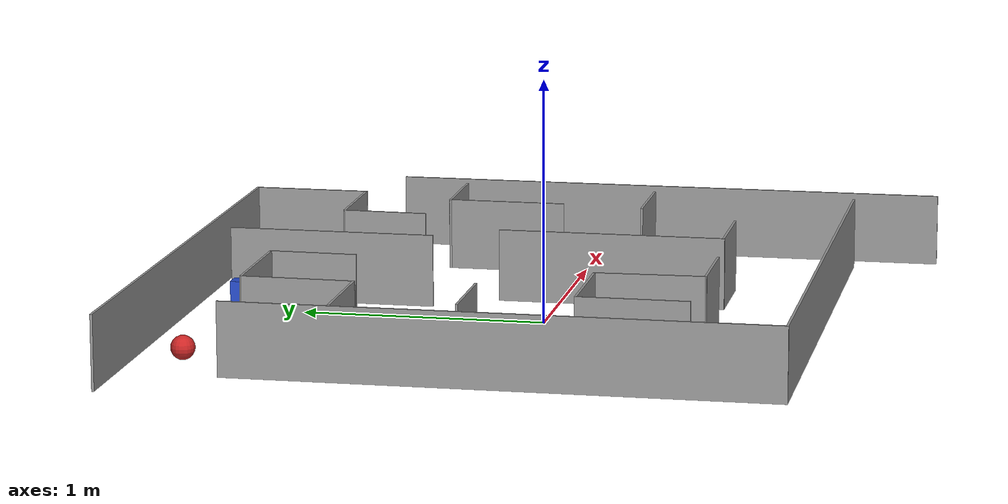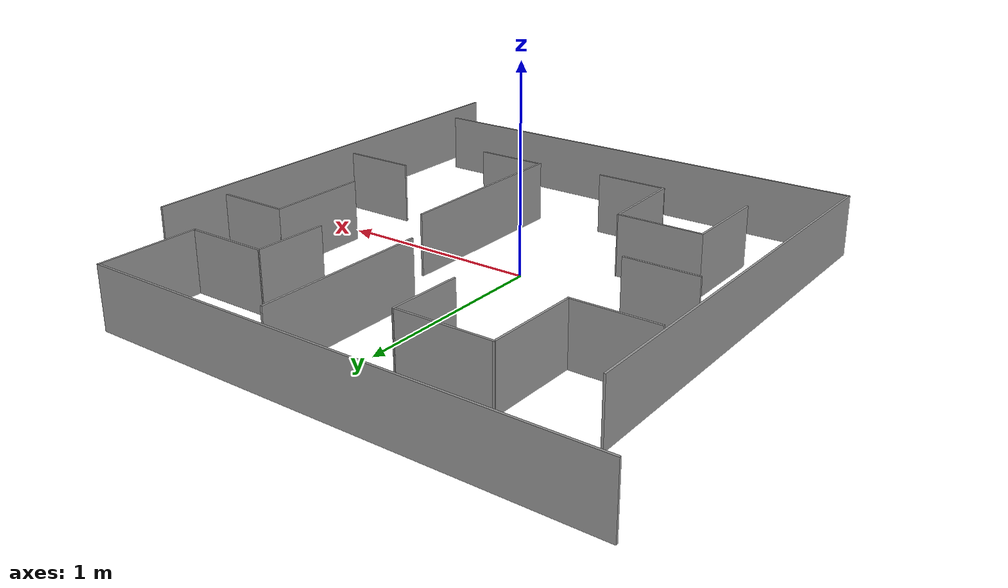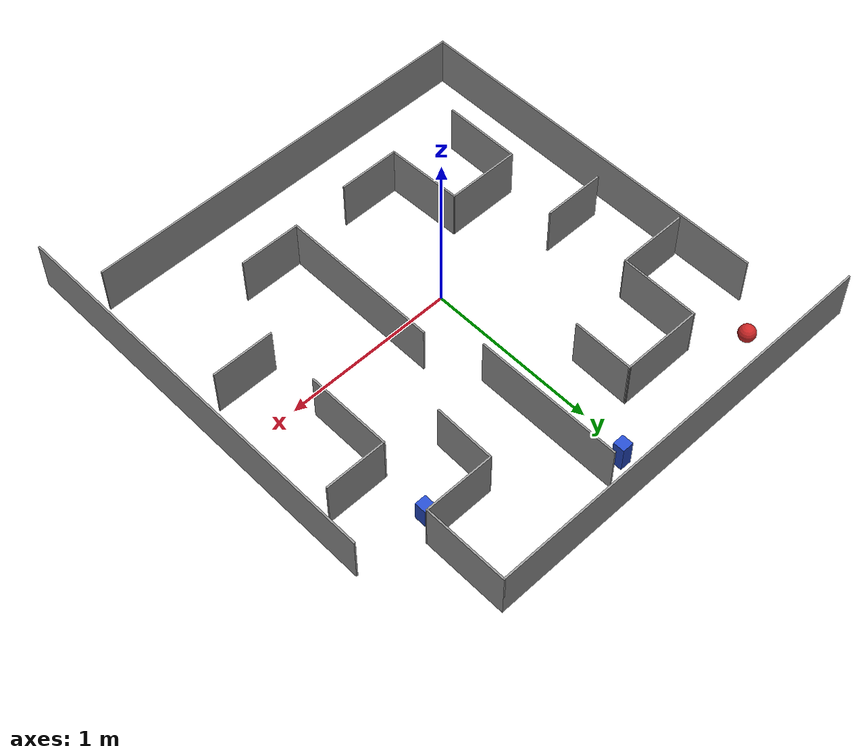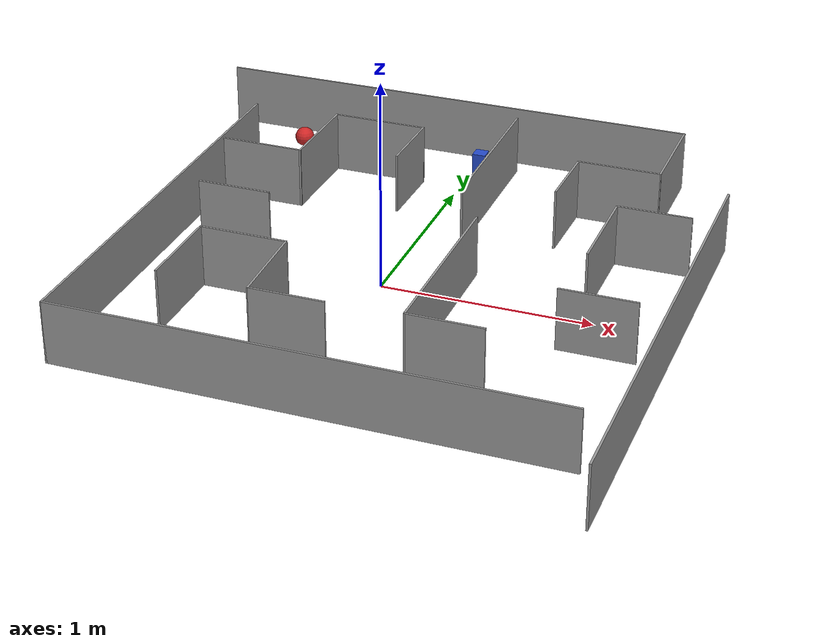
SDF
<?xml version='1.0'?>
<sdf version='1.7'>
  <model name='WorldTask3'>
    <model name='WorldTask3'>
      <link name='Wall_18'>
        <pose>-0.1745 1.47 0 0 -0 0</pose>
        <self_collide>0</self_collide>
        <enable_wind>0</enable_wind>
        <kinematic>0</kinematic>
        <visual name='Wall_18_Visual'>
          <pose>0 0 0.15 0 -0 0</pose>
          <geometry>
            <box>
              <size>2.436 0.01 0.3</size>
            </box>
          </geometry>
          <material>
            <script>
              <uri>file://media/materials/scripts/gazebo.material</uri>
              <name>Gazebo/Grey</name>
            </script>
            <ambient>1 1 1 1</ambient>
            <shader type='pixel'/>
          </material>
          <meta>
            <layer>0</layer>
          </meta>
          <transparency>0</transparency>
          <cast_shadows>1</cast_shadows>
        </visual>
        <collision name='Wall_18_Collision'>
          <laser_retro>0</laser_retro>
          <max_contacts>10</max_contacts>
          <pose>0 0 0.15 0 -0 0</pose>
          <geometry>
            <box>
              <size>2.436 0.01 0.3</size>
            </box>
          </geometry>
          <surface>
            <friction>
              <ode>
                <mu>1</mu>
                <mu2>1</mu2>
                <fdir1>0 0 0</fdir1>
                <slip1>0</slip1>
                <slip2>0</slip2>
              </ode>
              <torsional>
                <coefficient>1</coefficient>
                <patch_radius>0</patch_radius>
                <surface_radius>0</surface_radius>
                <use_patch_radius>1</use_patch_radius>
                <ode>
                  <slip>0</slip>
                </ode>
              </torsional>
            </friction>
            <bounce>
              <restitution_coefficient>0</restitution_coefficient>
              <threshold>1e+06</threshold>
            </bounce>
            <contact>
              <collide_without_contact>0</collide_without_contact>
              <collide_without_contact_bitmask>1</collide_without_contact_bitmask>
              <collide_bitmask>1</collide_bitmask>
              <ode>
                <soft_cfm>0</soft_cfm>
                <soft_erp>0.2</soft_erp>
                <kp>1e+13</kp>
                <kd>1</kd>
                <max_vel>0.01</max_vel>
                <min_depth>0</min_depth>
              </ode>
              <bullet>
                <split_impulse>1</split_impulse>
                <split_impulse_penetration_threshold>-0.01</split_impulse_penetration_threshold>
                <soft_cfm>0</soft_cfm>
                <soft_erp>0.2</soft_erp>
                <kp>1e+13</kp>
                <kd>1</kd>
              </bullet>
            </contact>
          </surface>
        </collision>
      </link>
      <link name='Wall_19'>
        <pose>1.0385 1.227 0 0 0 -1.5708</pose>
        <self_collide>0</self_collide>
        <enable_wind>0</enable_wind>
        <kinematic>0</kinematic>
        <visual name='Wall_19_Visual'>
          <pose>0 0 0.15 0 -0 0</pose>
          <geometry>
            <box>
              <size>0.496 0.01 0.3</size>
            </box>
          </geometry>
          <material>
            <script>
              <uri>file://media/materials/scripts/gazebo.material</uri>
              <name>Gazebo/Grey</name>
            </script>
            <ambient>1 1 1 1</ambient>
            <shader type='pixel'/>
          </material>
          <meta>
            <layer>0</layer>
          </meta>
          <transparency>0</transparency>
          <cast_shadows>1</cast_shadows>
        </visual>
        <collision name='Wall_19_Collision'>
          <laser_retro>0</laser_retro>
          <max_contacts>10</max_contacts>
          <pose>0 0 0.15 0 -0 0</pose>
          <geometry>
            <box>
              <size>0.496 0.01 0.3</size>
            </box>
          </geometry>
          <surface>
            <friction>
              <ode>
                <mu>1</mu>
                <mu2>1</mu2>
                <fdir1>0 0 0</fdir1>
                <slip1>0</slip1>
                <slip2>0</slip2>
              </ode>
              <torsional>
                <coefficient>1</coefficient>
                <patch_radius>0</patch_radius>
                <surface_radius>0</surface_radius>
                <use_patch_radius>1</use_patch_radius>
                <ode>
                  <slip>0</slip>
                </ode>
              </torsional>
            </friction>
            <bounce>
              <restitution_coefficient>0</restitution_coefficient>
              <threshold>1e+06</threshold>
            </bounce>
            <contact>
              <collide_without_contact>0</collide_without_contact>
              <collide_without_contact_bitmask>1</collide_without_contact_bitmask>
              <collide_bitmask>1</collide_bitmask>
              <ode>
                <soft_cfm>0</soft_cfm>
                <soft_erp>0.2</soft_erp>
                <kp>1e+13</kp>
                <kd>1</kd>
                <max_vel>0.01</max_vel>
                <min_depth>0</min_depth>
              </ode>
              <bullet>
                <split_impulse>1</split_impulse>
                <split_impulse_penetration_threshold>-0.01</split_impulse_penetration_threshold>
                <soft_cfm>0</soft_cfm>
                <soft_erp>0.2</soft_erp>
                <kp>1e+13</kp>
                <kd>1</kd>
              </bullet>
            </contact>
          </surface>
        </collision>
      </link>
      <link name='Wall_20'>
        <pose>0.837 0.9835 0 0 0 -3.13911</pose>
        <self_collide>0</self_collide>
        <enable_wind>0</enable_wind>
        <kinematic>0</kinematic>
        <visual name='Wall_20_Visual'>
          <pose>0 0 0.15 0 -0 0</pose>
          <geometry>
            <box>
              <size>0.413001 0.01 0.3</size>
            </box>
          </geometry>
          <material>
            <script>
              <uri>file://media/materials/scripts/gazebo.material</uri>
              <name>Gazebo/Grey</name>
            </script>
            <ambient>1 1 1 1</ambient>
            <shader type='pixel'/>
          </material>
          <meta>
            <layer>0</layer>
          </meta>
          <transparency>0</transparency>
          <cast_shadows>1</cast_shadows>
        </visual>
        <collision name='Wall_20_Collision'>
          <laser_retro>0</laser_retro>
          <max_contacts>10</max_contacts>
          <pose>0 0 0.15 0 -0 0</pose>
          <geometry>
            <box>
              <size>0.413001 0.01 0.3</size>
            </box>
          </geometry>
          <surface>
            <friction>
              <ode>
                <mu>1</mu>
                <mu2>1</mu2>
                <fdir1>0 0 0</fdir1>
                <slip1>0</slip1>
                <slip2>0</slip2>
              </ode>
              <torsional>
                <coefficient>1</coefficient>
                <patch_radius>0</patch_radius>
                <surface_radius>0</surface_radius>
                <use_patch_radius>1</use_patch_radius>
                <ode>
                  <slip>0</slip>
                </ode>
              </torsional>
            </friction>
            <bounce>
              <restitution_coefficient>0</restitution_coefficient>
              <threshold>1e+06</threshold>
            </bounce>
            <contact>
              <collide_without_contact>0</collide_without_contact>
              <collide_without_contact_bitmask>1</collide_without_contact_bitmask>
              <collide_bitmask>1</collide_bitmask>
              <ode>
                <soft_cfm>0</soft_cfm>
                <soft_erp>0.2</soft_erp>
                <kp>1e+13</kp>
                <kd>1</kd>
                <max_vel>0.01</max_vel>
                <min_depth>0</min_depth>
              </ode>
              <bullet>
                <split_impulse>1</split_impulse>
                <split_impulse_penetration_threshold>-0.01</split_impulse_penetration_threshold>
                <soft_cfm>0</soft_cfm>
                <soft_erp>0.2</soft_erp>
                <kp>1e+13</kp>
                <kd>1</kd>
              </bullet>
            </contact>
          </surface>
        </collision>
      </link>
      <link name='Wall_21'>
        <pose>0.6315 0.808 0 0 0 -1.59365</pose>
        <self_collide>0</self_collide>
        <enable_wind>0</enable_wind>
        <kinematic>0</kinematic>
        <visual name='Wall_21_Visual'>
          <pose>0 0 0.15 0 -0 0</pose>
          <geometry>
            <box>
              <size>0.360091 0.01 0.3</size>
            </box>
          </geometry>
          <material>
            <script>
              <uri>file://media/materials/scripts/gazebo.material</uri>
              <name>Gazebo/Grey</name>
            </script>
            <ambient>1 1 1 1</ambient>
            <shader type='pixel'/>
          </material>
          <meta>
            <layer>0</layer>
          </meta>
          <transparency>0</transparency>
          <cast_shadows>1</cast_shadows>
        </visual>
        <collision name='Wall_21_Collision'>
          <laser_retro>0</laser_retro>
          <max_contacts>10</max_contacts>
          <pose>0 0 0.15 0 -0 0</pose>
          <geometry>
            <box>
              <size>0.360091 0.01 0.3</size>
            </box>
          </geometry>
          <surface>
            <friction>
              <ode>
                <mu>1</mu>
                <mu2>1</mu2>
                <fdir1>0 0 0</fdir1>
                <slip1>0</slip1>
                <slip2>0</slip2>
              </ode>
              <torsional>
                <coefficient>1</coefficient>
                <patch_radius>0</patch_radius>
                <surface_radius>0</surface_radius>
                <use_patch_radius>1</use_patch_radius>
                <ode>
                  <slip>0</slip>
                </ode>
              </torsional>
            </friction>
            <bounce>
              <restitution_coefficient>0</restitution_coefficient>
              <threshold>1e+06</threshold>
            </bounce>
            <contact>
              <collide_without_contact>0</collide_without_contact>
              <collide_without_contact_bitmask>1</collide_without_contact_bitmask>
              <collide_bitmask>1</collide_bitmask>
              <ode>
                <soft_cfm>0</soft_cfm>
                <soft_erp>0.2</soft_erp>
                <kp>1e+13</kp>
                <kd>1</kd>
                <max_vel>0.01</max_vel>
                <min_depth>0</min_depth>
              </ode>
              <bullet>
                <split_impulse>1</split_impulse>
                <split_impulse_penetration_threshold>-0.01</split_impulse_penetration_threshold>
                <soft_cfm>0</soft_cfm>
                <soft_erp>0.2</soft_erp>
                <kp>1e+13</kp>
                <kd>1</kd>
              </bullet>
            </contact>
          </surface>
        </collision>
      </link>
      <link name='Wall_23'>
        <pose>1.3875 -0.295 0 0 0 -1.5708</pose>
        <self_collide>0</self_collide>
        <enable_wind>0</enable_wind>
        <kinematic>0</kinematic>
        <visual name='Wall_23_Visual'>
          <pose>0 0 0.15 0 -0 0</pose>
          <geometry>
            <box>
              <size>2.36 0.01 0.3</size>
            </box>
          </geometry>
          <material>
            <script>
              <uri>file://media/materials/scripts/gazebo.material</uri>
              <name>Gazebo/Grey</name>
            </script>
            <ambient>1 1 1 1</ambient>
            <shader type='pixel'/>
          </material>
          <meta>
            <layer>0</layer>
          </meta>
          <transparency>0</transparency>
          <cast_shadows>1</cast_shadows>
        </visual>
        <collision name='Wall_23_Collision'>
          <laser_retro>0</laser_retro>
          <max_contacts>10</max_contacts>
          <pose>0 0 0.15 0 -0 0</pose>
          <geometry>
            <box>
              <size>2.36 0.01 0.3</size>
            </box>
          </geometry>
          <surface>
            <friction>
              <ode>
                <mu>1</mu>
                <mu2>1</mu2>
                <fdir1>0 0 0</fdir1>
                <slip1>0</slip1>
                <slip2>0</slip2>
              </ode>
              <torsional>
                <coefficient>1</coefficient>
                <patch_radius>0</patch_radius>
                <surface_radius>0</surface_radius>
                <use_patch_radius>1</use_patch_radius>
                <ode>
                  <slip>0</slip>
                </ode>
              </torsional>
            </friction>
            <bounce>
              <restitution_coefficient>0</restitution_coefficient>
              <threshold>1e+06</threshold>
            </bounce>
            <contact>
              <collide_without_contact>0</collide_without_contact>
              <collide_without_contact_bitmask>1</collide_without_contact_bitmask>
              <collide_bitmask>1</collide_bitmask>
              <ode>
                <soft_cfm>0</soft_cfm>
                <soft_erp>0.2</soft_erp>
                <kp>1e+13</kp>
                <kd>1</kd>
                <max_vel>0.01</max_vel>
                <min_depth>0</min_depth>
              </ode>
              <bullet>
                <split_impulse>1</split_impulse>
                <split_impulse_penetration_threshold>-0.01</split_impulse_penetration_threshold>
                <soft_cfm>0</soft_cfm>
                <soft_erp>0.2</soft_erp>
                <kp>1e+13</kp>
                <kd>1</kd>
              </bullet>
            </contact>
          </surface>
        </collision>
      </link>
      <link name='Wall_25'>
        <pose>0.0825 -1.124 0 0 -0 0</pose>
        <self_collide>0</self_collide>
        <enable_wind>0</enable_wind>
        <kinematic>0</kinematic>
        <visual name='Wall_25_Visual'>
          <pose>0 0 0.15 0 -0 0</pose>
          <geometry>
            <box>
              <size>2.36 0.01 0.3</size>
            </box>
          </geometry>
          <material>
            <script>
              <uri>file://media/materials/scripts/gazebo.material</uri>
              <name>Gazebo/Grey</name>
            </script>
            <ambient>1 1 1 1</ambient>
            <shader type='pixel'/>
          </material>
          <meta>
            <layer>0</layer>
          </meta>
          <transparency>0</transparency>
          <cast_shadows>1</cast_shadows>
        </visual>
        <collision name='Wall_25_Collision'>
          <laser_retro>0</laser_retro>
          <max_contacts>10</max_contacts>
          <pose>0 0 0.15 0 -0 0</pose>
          <geometry>
            <box>
              <size>2.36 0.01 0.3</size>
            </box>
          </geometry>
          <surface>
            <friction>
              <ode>
                <mu>1</mu>
                <mu2>1</mu2>
                <fdir1>0 0 0</fdir1>
                <slip1>0</slip1>
                <slip2>0</slip2>
              </ode>
              <torsional>
                <coefficient>1</coefficient>
                <patch_radius>0</patch_radius>
                <surface_radius>0</surface_radius>
                <use_patch_radius>1</use_patch_radius>
                <ode>
                  <slip>0</slip>
                </ode>
              </torsional>
            </friction>
            <bounce>
              <restitution_coefficient>0</restitution_coefficient>
              <threshold>1e+06</threshold>
            </bounce>
            <contact>
              <collide_without_contact>0</collide_without_contact>
              <collide_without_contact_bitmask>1</collide_without_contact_bitmask>
              <collide_bitmask>1</collide_bitmask>
              <ode>
                <soft_cfm>0</soft_cfm>
                <soft_erp>0.2</soft_erp>
                <kp>1e+13</kp>
                <kd>1</kd>
                <max_vel>0.01</max_vel>
                <min_depth>0</min_depth>
              </ode>
              <bullet>
                <split_impulse>1</split_impulse>
                <split_impulse_penetration_threshold>-0.01</split_impulse_penetration_threshold>
                <soft_cfm>0</soft_cfm>
                <soft_erp>0.2</soft_erp>
                <kp>1e+13</kp>
                <kd>1</kd>
              </bullet>
            </contact>
          </surface>
        </collision>
      </link>
      <link name='Wall_27'>
        <pose>-1.0925 -0.031 0 0 0 -1.5708</pose>
        <self_collide>0</self_collide>
        <enable_wind>0</enable_wind>
        <kinematic>0</kinematic>
        <visual name='Wall_27_Visual'>
          <pose>0 0 0.15 0 -0 0</pose>
          <geometry>
            <box>
              <size>2.196 0.01 0.3</size>
            </box>
          </geometry>
          <material>
            <script>
              <uri>file://media/materials/scripts/gazebo.material</uri>
              <name>Gazebo/Grey</name>
            </script>
            <ambient>1 1 1 1</ambient>
            <shader type='pixel'/>
          </material>
          <meta>
            <layer>0</layer>
          </meta>
          <transparency>0</transparency>
          <cast_shadows>1</cast_shadows>
        </visual>
        <collision name='Wall_27_Collision'>
          <laser_retro>0</laser_retro>
          <max_contacts>10</max_contacts>
          <pose>0 0 0.15 0 -0 0</pose>
          <geometry>
            <box>
              <size>2.196 0.01 0.3</size>
            </box>
          </geometry>
          <surface>
            <friction>
              <ode>
                <mu>1</mu>
                <mu2>1</mu2>
                <fdir1>0 0 0</fdir1>
                <slip1>0</slip1>
                <slip2>0</slip2>
              </ode>
              <torsional>
                <coefficient>1</coefficient>
                <patch_radius>0</patch_radius>
                <surface_radius>0</surface_radius>
                <use_patch_radius>1</use_patch_radius>
                <ode>
                  <slip>0</slip>
                </ode>
              </torsional>
            </friction>
            <bounce>
              <restitution_coefficient>0</restitution_coefficient>
              <threshold>1e+06</threshold>
            </bounce>
            <contact>
              <collide_without_contact>0</collide_without_contact>
              <collide_without_contact_bitmask>1</collide_without_contact_bitmask>
              <collide_bitmask>1</collide_bitmask>
              <ode>
                <soft_cfm>0</soft_cfm>
                <soft_erp>0.2</soft_erp>
                <kp>1e+13</kp>
                <kd>1</kd>
                <max_vel>0.01</max_vel>
                <min_depth>0</min_depth>
              </ode>
              <bullet>
                <split_impulse>1</split_impulse>
                <split_impulse_penetration_threshold>-0.01</split_impulse_penetration_threshold>
                <soft_cfm>0</soft_cfm>
                <soft_erp>0.2</soft_erp>
                <kp>1e+13</kp>
                <kd>1</kd>
              </bullet>
            </contact>
          </surface>
        </collision>
      </link>
      <link name='Wall_29'>
        <pose>-0.8685 0.631 0 0 -0 0</pose>
        <self_collide>0</self_collide>
        <enable_wind>0</enable_wind>
        <kinematic>0</kinematic>
        <visual name='Wall_29_Visual'>
          <pose>0 0 0.15 0 -0 0</pose>
          <geometry>
            <box>
              <size>0.412 0.01 0.3</size>
            </box>
          </geometry>
          <material>
            <script>
              <uri>file://media/materials/scripts/gazebo.material</uri>
              <name>Gazebo/Grey</name>
            </script>
            <ambient>1 1 1 1</ambient>
            <shader type='pixel'/>
          </material>
          <meta>
            <layer>0</layer>
          </meta>
          <transparency>0</transparency>
          <cast_shadows>1</cast_shadows>
        </visual>
        <collision name='Wall_29_Collision'>
          <laser_retro>0</laser_retro>
          <max_contacts>10</max_contacts>
          <pose>0 0 0.15 0 -0 0</pose>
          <geometry>
            <box>
              <size>0.412 0.01 0.3</size>
            </box>
          </geometry>
          <surface>
            <friction>
              <ode>
                <mu>1</mu>
                <mu2>1</mu2>
                <fdir1>0 0 0</fdir1>
                <slip1>0</slip1>
                <slip2>0</slip2>
              </ode>
              <torsional>
                <coefficient>1</coefficient>
                <patch_radius>0</patch_radius>
                <surface_radius>0</surface_radius>
                <use_patch_radius>1</use_patch_radius>
                <ode>
                  <slip>0</slip>
                </ode>
              </torsional>
            </friction>
            <bounce>
              <restitution_coefficient>0</restitution_coefficient>
              <threshold>1e+06</threshold>
            </bounce>
            <contact>
              <collide_without_contact>0</collide_without_contact>
              <collide_without_contact_bitmask>1</collide_without_contact_bitmask>
              <collide_bitmask>1</collide_bitmask>
              <ode>
                <soft_cfm>0</soft_cfm>
                <soft_erp>0.2</soft_erp>
                <kp>1e+13</kp>
                <kd>1</kd>
                <max_vel>0.01</max_vel>
                <min_depth>0</min_depth>
              </ode>
              <bullet>
                <split_impulse>1</split_impulse>
                <split_impulse_penetration_threshold>-0.01</split_impulse_penetration_threshold>
                <soft_cfm>0</soft_cfm>
                <soft_erp>0.2</soft_erp>
                <kp>1e+13</kp>
                <kd>1</kd>
              </bullet>
            </contact>
          </surface>
        </collision>
      </link>
      <link name='Wall_33'>
        <pose>-0.6635 0.859 0 0 0 -1.58834</pose>
        <self_collide>0</self_collide>
        <enable_wind>0</enable_wind>
        <kinematic>0</kinematic>
        <visual name='Wall_33_Visual'>
          <pose>0 0 0.15 0 -0 0</pose>
          <geometry>
            <box>
              <size>0.466265 0.01 0.3</size>
            </box>
          </geometry>
          <material>
            <script>
              <uri>file://media/materials/scripts/gazebo.material</uri>
              <name>Gazebo/Grey</name>
            </script>
            <ambient>1 1 1 1</ambient>
            <shader type='pixel'/>
          </material>
          <meta>
            <layer>0</layer>
          </meta>
          <transparency>0</transparency>
          <cast_shadows>1</cast_shadows>
        </visual>
        <collision name='Wall_33_Collision'>
          <laser_retro>0</laser_retro>
          <max_contacts>10</max_contacts>
          <pose>0 0 0.15 0 -0 0</pose>
          <geometry>
            <box>
              <size>0.466265 0.01 0.3</size>
            </box>
          </geometry>
          <surface>
            <friction>
              <ode>
                <mu>1</mu>
                <mu2>1</mu2>
                <fdir1>0 0 0</fdir1>
                <slip1>0</slip1>
                <slip2>0</slip2>
              </ode>
              <torsional>
                <coefficient>1</coefficient>
                <patch_radius>0</patch_radius>
                <surface_radius>0</surface_radius>
                <use_patch_radius>1</use_patch_radius>
                <ode>
                  <slip>0</slip>
                </ode>
              </torsional>
            </friction>
            <bounce>
              <restitution_coefficient>0</restitution_coefficient>
              <threshold>1e+06</threshold>
            </bounce>
            <contact>
              <collide_without_contact>0</collide_without_contact>
              <collide_without_contact_bitmask>1</collide_without_contact_bitmask>
              <collide_bitmask>1</collide_bitmask>
              <ode>
                <soft_cfm>0</soft_cfm>
                <soft_erp>0.2</soft_erp>
                <kp>1e+13</kp>
                <kd>1</kd>
                <max_vel>0.01</max_vel>
                <min_depth>0</min_depth>
              </ode>
              <bullet>
                <split_impulse>1</split_impulse>
                <split_impulse_penetration_threshold>-0.01</split_impulse_penetration_threshold>
                <soft_cfm>0</soft_cfm>
                <soft_erp>0.2</soft_erp>
                <kp>1e+13</kp>
                <kd>1</kd>
              </bullet>
            </contact>
          </surface>
        </collision>
      </link>
      <link name='Wall_36'>
        <pose>-0.428 1.087 0 0 -0 3.14159</pose>
        <self_collide>0</self_collide>
        <enable_wind>0</enable_wind>
        <kinematic>0</kinematic>
        <visual name='Wall_36_Visual'>
          <pose>0 0 0.15 0 -0 0</pose>
          <geometry>
            <box>
              <size>0.473 0.01 0.3</size>
            </box>
          </geometry>
          <material>
            <script>
              <uri>file://media/materials/scripts/gazebo.material</uri>
              <name>Gazebo/Grey</name>
            </script>
            <ambient>1 1 1 1</ambient>
            <shader type='pixel'/>
          </material>
          <meta>
            <layer>0</layer>
          </meta>
          <transparency>0</transparency>
          <cast_shadows>1</cast_shadows>
        </visual>
        <collision name='Wall_36_Collision'>
          <laser_retro>0</laser_retro>
          <max_contacts>10</max_contacts>
          <pose>0 0 0.15 0 -0 0</pose>
          <geometry>
            <box>
              <size>0.473 0.01 0.3</size>
            </box>
          </geometry>
          <surface>
            <friction>
              <ode>
                <mu>1</mu>
                <mu2>1</mu2>
                <fdir1>0 0 0</fdir1>
                <slip1>0</slip1>
                <slip2>0</slip2>
              </ode>
              <torsional>
                <coefficient>1</coefficient>
                <patch_radius>0</patch_radius>
                <surface_radius>0</surface_radius>
                <use_patch_radius>1</use_patch_radius>
                <ode>
                  <slip>0</slip>
                </ode>
              </torsional>
            </friction>
            <bounce>
              <restitution_coefficient>0</restitution_coefficient>
              <threshold>1e+06</threshold>
            </bounce>
            <contact>
              <collide_without_contact>0</collide_without_contact>
              <collide_without_contact_bitmask>1</collide_without_contact_bitmask>
              <collide_bitmask>1</collide_bitmask>
              <ode>
                <soft_cfm>0</soft_cfm>
                <soft_erp>0.2</soft_erp>
                <kp>1e+13</kp>
                <kd>1</kd>
                <max_vel>0.01</max_vel>
                <min_depth>0</min_depth>
              </ode>
              <bullet>
                <split_impulse>1</split_impulse>
                <split_impulse_penetration_threshold>-0.01</split_impulse_penetration_threshold>
                <soft_cfm>0</soft_cfm>
                <soft_erp>0.2</soft_erp>
                <kp>1e+13</kp>
                <kd>1</kd>
              </bullet>
            </contact>
          </surface>
        </collision>
      </link>
      <link name='Wall_38'>
        <pose>-0.2 0.912 0 0 0 -1.59079</pose>
        <self_collide>0</self_collide>
        <enable_wind>0</enable_wind>
        <kinematic>0</kinematic>
        <visual name='Wall_38_Visual'>
          <pose>0 0 0.15 0 -0 0</pose>
          <geometry>
            <box>
              <size>0.36007 0.01 0.3</size>
            </box>
          </geometry>
          <material>
            <script>
              <uri>file://media/materials/scripts/gazebo.material</uri>
              <name>Gazebo/Grey</name>
            </script>
            <ambient>1 1 1 1</ambient>
            <shader type='pixel'/>
          </material>
          <meta>
            <layer>0</layer>
          </meta>
          <transparency>0</transparency>
          <cast_shadows>1</cast_shadows>
        </visual>
        <collision name='Wall_38_Collision'>
          <laser_retro>0</laser_retro>
          <max_contacts>10</max_contacts>
          <pose>0 0 0.15 0 -0 0</pose>
          <geometry>
            <box>
              <size>0.36007 0.01 0.3</size>
            </box>
          </geometry>
          <surface>
            <friction>
              <ode>
                <mu>1</mu>
                <mu2>1</mu2>
                <fdir1>0 0 0</fdir1>
                <slip1>0</slip1>
                <slip2>0</slip2>
              </ode>
              <torsional>
                <coefficient>1</coefficient>
                <patch_radius>0</patch_radius>
                <surface_radius>0</surface_radius>
                <use_patch_radius>1</use_patch_radius>
                <ode>
                  <slip>0</slip>
                </ode>
              </torsional>
            </friction>
            <bounce>
              <restitution_coefficient>0</restitution_coefficient>
              <threshold>1e+06</threshold>
            </bounce>
            <contact>
              <collide_without_contact>0</collide_without_contact>
              <collide_without_contact_bitmask>1</collide_without_contact_bitmask>
              <collide_bitmask>1</collide_bitmask>
              <ode>
                <soft_cfm>0</soft_cfm>
                <soft_erp>0.2</soft_erp>
                <kp>1e+13</kp>
                <kd>1</kd>
                <max_vel>0.01</max_vel>
                <min_depth>0</min_depth>
              </ode>
              <bullet>
                <split_impulse>1</split_impulse>
                <split_impulse_penetration_threshold>-0.01</split_impulse_penetration_threshold>
                <soft_cfm>0</soft_cfm>
                <soft_erp>0.2</soft_erp>
                <kp>1e+13</kp>
                <kd>1</kd>
              </bullet>
            </contact>
          </surface>
        </collision>
      </link>
      <link name='Wall_40'>
        <pose>-0.7985 0.154 0 0 -0 3.14159</pose>
        <self_collide>0</self_collide>
        <enable_wind>0</enable_wind>
        <kinematic>0</kinematic>
        <visual name='Wall_40_Visual'>
          <pose>0 0 0.15 0 -0 0</pose>
          <geometry>
            <box>
              <size>0.36 0.01 0.3</size>
            </box>
          </geometry>
          <material>
            <script>
              <uri>file://media/materials/scripts/gazebo.material</uri>
              <name>Gazebo/Grey</name>
            </script>
            <ambient>1 1 1 1</ambient>
            <shader type='pixel'/>
          </material>
          <meta>
            <layer>0</layer>
          </meta>
          <transparency>0</transparency>
          <cast_shadows>1</cast_shadows>
        </visual>
        <collision name='Wall_40_Collision'>
          <laser_retro>0</laser_retro>
          <max_contacts>10</max_contacts>
          <pose>0 0 0.15 0 -0 0</pose>
          <geometry>
            <box>
              <size>0.36 0.01 0.3</size>
            </box>
          </geometry>
          <surface>
            <friction>
              <ode>
                <mu>1</mu>
                <mu2>1</mu2>
                <fdir1>0 0 0</fdir1>
                <slip1>0</slip1>
                <slip2>0</slip2>
              </ode>
              <torsional>
                <coefficient>1</coefficient>
                <patch_radius>0</patch_radius>
                <surface_radius>0</surface_radius>
                <use_patch_radius>1</use_patch_radius>
                <ode>
                  <slip>0</slip>
                </ode>
              </torsional>
            </friction>
            <bounce>
              <restitution_coefficient>0</restitution_coefficient>
              <threshold>1e+06</threshold>
            </bounce>
            <contact>
              <collide_without_contact>0</collide_without_contact>
              <collide_without_contact_bitmask>1</collide_without_contact_bitmask>
              <collide_bitmask>1</collide_bitmask>
              <ode>
                <soft_cfm>0</soft_cfm>
                <soft_erp>0.2</soft_erp>
                <kp>1e+13</kp>
                <kd>1</kd>
                <max_vel>0.01</max_vel>
                <min_depth>0</min_depth>
              </ode>
              <bullet>
                <split_impulse>1</split_impulse>
                <split_impulse_penetration_threshold>-0.01</split_impulse_penetration_threshold>
                <soft_cfm>0</soft_cfm>
                <soft_erp>0.2</soft_erp>
                <kp>1e+13</kp>
                <kd>1</kd>
              </bullet>
            </contact>
          </surface>
        </collision>
      </link>
      <link name='Wall_42'>
        <pose>-0.7675 -0.4875 0 0 -0 1.5708</pose>
        <self_collide>0</self_collide>
        <enable_wind>0</enable_wind>
        <kinematic>0</kinematic>
        <visual name='Wall_42_Visual'>
          <pose>0 0 0.15 0 -0 0</pose>
          <geometry>
            <box>
              <size>0.451 0.01 0.3</size>
            </box>
          </geometry>
          <material>
            <script>
              <uri>file://media/materials/scripts/gazebo.material</uri>
              <name>Gazebo/Grey</name>
            </script>
            <ambient>1 1 1 1</ambient>
            <shader type='pixel'/>
          </material>
          <meta>
            <layer>0</layer>
          </meta>
          <transparency>0</transparency>
          <cast_shadows>1</cast_shadows>
        </visual>
        <collision name='Wall_42_Collision'>
          <laser_retro>0</laser_retro>
          <max_contacts>10</max_contacts>
          <pose>0 0 0.15 0 -0 0</pose>
          <geometry>
            <box>
              <size>0.451 0.01 0.3</size>
            </box>
          </geometry>
          <surface>
            <friction>
              <ode>
                <mu>1</mu>
                <mu2>1</mu2>
                <fdir1>0 0 0</fdir1>
                <slip1>0</slip1>
                <slip2>0</slip2>
              </ode>
              <torsional>
                <coefficient>1</coefficient>
                <patch_radius>0</patch_radius>
                <surface_radius>0</surface_radius>
                <use_patch_radius>1</use_patch_radius>
                <ode>
                  <slip>0</slip>
                </ode>
              </torsional>
            </friction>
            <bounce>
              <restitution_coefficient>0</restitution_coefficient>
              <threshold>1e+06</threshold>
            </bounce>
            <contact>
              <collide_without_contact>0</collide_without_contact>
              <collide_without_contact_bitmask>1</collide_without_contact_bitmask>
              <collide_bitmask>1</collide_bitmask>
              <ode>
                <soft_cfm>0</soft_cfm>
                <soft_erp>0.2</soft_erp>
                <kp>1e+13</kp>
                <kd>1</kd>
                <max_vel>0.01</max_vel>
                <min_depth>0</min_depth>
              </ode>
              <bullet>
                <split_impulse>1</split_impulse>
                <split_impulse_penetration_threshold>-0.01</split_impulse_penetration_threshold>
                <soft_cfm>0</soft_cfm>
                <soft_erp>0.2</soft_erp>
                <kp>1e+13</kp>
                <kd>1</kd>
              </bullet>
            </contact>
          </surface>
        </collision>
      </link>
      <link name='Wall_44'>
        <pose>-0.5585 -0.267 0 0 -0 3.14159</pose>
        <self_collide>0</self_collide>
        <enable_wind>0</enable_wind>
        <kinematic>0</kinematic>
        <visual name='Wall_44_Visual'>
          <pose>0 0 0.15 0 -0 0</pose>
          <geometry>
            <box>
              <size>0.428 0.01 0.3</size>
            </box>
          </geometry>
          <material>
            <script>
              <uri>file://media/materials/scripts/gazebo.material</uri>
              <name>Gazebo/Grey</name>
            </script>
            <ambient>1 1 1 1</ambient>
            <shader type='pixel'/>
          </material>
          <meta>
            <layer>0</layer>
          </meta>
          <transparency>0</transparency>
          <cast_shadows>1</cast_shadows>
        </visual>
        <collision name='Wall_44_Collision'>
          <laser_retro>0</laser_retro>
          <max_contacts>10</max_contacts>
          <pose>0 0 0.15 0 -0 0</pose>
          <geometry>
            <box>
              <size>0.428 0.01 0.3</size>
            </box>
          </geometry>
          <surface>
            <friction>
              <ode>
                <mu>1</mu>
                <mu2>1</mu2>
                <fdir1>0 0 0</fdir1>
                <slip1>0</slip1>
                <slip2>0</slip2>
              </ode>
              <torsional>
                <coefficient>1</coefficient>
                <patch_radius>0</patch_radius>
                <surface_radius>0</surface_radius>
                <use_patch_radius>1</use_patch_radius>
                <ode>
                  <slip>0</slip>
                </ode>
              </torsional>
            </friction>
            <bounce>
              <restitution_coefficient>0</restitution_coefficient>
              <threshold>1e+06</threshold>
            </bounce>
            <contact>
              <collide_without_contact>0</collide_without_contact>
              <collide_without_contact_bitmask>1</collide_without_contact_bitmask>
              <collide_bitmask>1</collide_bitmask>
              <ode>
                <soft_cfm>0</soft_cfm>
                <soft_erp>0.2</soft_erp>
                <kp>1e+13</kp>
                <kd>1</kd>
                <max_vel>0.01</max_vel>
                <min_depth>0</min_depth>
              </ode>
              <bullet>
                <split_impulse>1</split_impulse>
                <split_impulse_penetration_threshold>-0.01</split_impulse_penetration_threshold>
                <soft_cfm>0</soft_cfm>
                <soft_erp>0.2</soft_erp>
                <kp>1e+13</kp>
                <kd>1</kd>
              </bullet>
            </contact>
          </surface>
        </collision>
      </link>
      <link name='Wall_46'>
        <pose>-0.342 -0.4875 0 0 -0 1.6048</pose>
        <self_collide>0</self_collide>
        <enable_wind>0</enable_wind>
        <kinematic>0</kinematic>
        <visual name='Wall_46_Visual'>
          <pose>0 0 0.15 0 -0 0</pose>
          <geometry>
            <box>
              <size>0.451255 0.01 0.3</size>
            </box>
          </geometry>
          <material>
            <script>
              <uri>file://media/materials/scripts/gazebo.material</uri>
              <name>Gazebo/Grey</name>
            </script>
            <ambient>1 1 1 1</ambient>
            <shader type='pixel'/>
          </material>
          <meta>
            <layer>0</layer>
          </meta>
          <transparency>0</transparency>
          <cast_shadows>1</cast_shadows>
        </visual>
        <collision name='Wall_46_Collision'>
          <laser_retro>0</laser_retro>
          <max_contacts>10</max_contacts>
          <pose>0 0 0.15 0 -0 0</pose>
          <geometry>
            <box>
              <size>0.451255 0.01 0.3</size>
            </box>
          </geometry>
          <surface>
            <friction>
              <ode>
                <mu>1</mu>
                <mu2>1</mu2>
                <fdir1>0 0 0</fdir1>
                <slip1>0</slip1>
                <slip2>0</slip2>
              </ode>
              <torsional>
                <coefficient>1</coefficient>
                <patch_radius>0</patch_radius>
                <surface_radius>0</surface_radius>
                <use_patch_radius>1</use_patch_radius>
                <ode>
                  <slip>0</slip>
                </ode>
              </torsional>
            </friction>
            <bounce>
              <restitution_coefficient>0</restitution_coefficient>
              <threshold>1e+06</threshold>
            </bounce>
            <contact>
              <collide_without_contact>0</collide_without_contact>
              <collide_without_contact_bitmask>1</collide_without_contact_bitmask>
              <collide_bitmask>1</collide_bitmask>
              <ode>
                <soft_cfm>0</soft_cfm>
                <soft_erp>0.2</soft_erp>
                <kp>1e+13</kp>
                <kd>1</kd>
                <max_vel>0.01</max_vel>
                <min_depth>0</min_depth>
              </ode>
              <bullet>
                <split_impulse>1</split_impulse>
                <split_impulse_penetration_threshold>-0.01</split_impulse_penetration_threshold>
                <soft_cfm>0</soft_cfm>
                <soft_erp>0.2</soft_erp>
                <kp>1e+13</kp>
                <kd>1</kd>
              </bullet>
            </contact>
          </surface>
        </collision>
      </link>
      <link name='Wall_48'>
        <pose>-0.1595 -0.708 0 0 -0 3.14159</pose>
        <self_collide>0</self_collide>
        <enable_wind>0</enable_wind>
        <kinematic>0</kinematic>
        <visual name='Wall_48_Visual'>
          <pose>0 0 0.15 0 -0 0</pose>
          <geometry>
            <box>
              <size>0.36 0.01 0.3</size>
            </box>
          </geometry>
          <material>
            <script>
              <uri>file://media/materials/scripts/gazebo.material</uri>
              <name>Gazebo/Grey</name>
            </script>
            <ambient>1 1 1 1</ambient>
            <shader type='pixel'/>
          </material>
          <meta>
            <layer>0</layer>
          </meta>
          <transparency>0</transparency>
          <cast_shadows>1</cast_shadows>
        </visual>
        <collision name='Wall_48_Collision'>
          <laser_retro>0</laser_retro>
          <max_contacts>10</max_contacts>
          <pose>0 0 0.15 0 -0 0</pose>
          <geometry>
            <box>
              <size>0.36 0.01 0.3</size>
            </box>
          </geometry>
          <surface>
            <friction>
              <ode>
                <mu>1</mu>
                <mu2>1</mu2>
                <fdir1>0 0 0</fdir1>
                <slip1>0</slip1>
                <slip2>0</slip2>
              </ode>
              <torsional>
                <coefficient>1</coefficient>
                <patch_radius>0</patch_radius>
                <surface_radius>0</surface_radius>
                <use_patch_radius>1</use_patch_radius>
                <ode>
                  <slip>0</slip>
                </ode>
              </torsional>
            </friction>
            <bounce>
              <restitution_coefficient>0</restitution_coefficient>
              <threshold>1e+06</threshold>
            </bounce>
            <contact>
              <collide_without_contact>0</collide_without_contact>
              <collide_without_contact_bitmask>1</collide_without_contact_bitmask>
              <collide_bitmask>1</collide_bitmask>
              <ode>
                <soft_cfm>0</soft_cfm>
                <soft_erp>0.2</soft_erp>
                <kp>1e+13</kp>
                <kd>1</kd>
                <max_vel>0.01</max_vel>
                <min_depth>0</min_depth>
              </ode>
              <bullet>
                <split_impulse>1</split_impulse>
                <split_impulse_penetration_threshold>-0.01</split_impulse_penetration_threshold>
                <soft_cfm>0</soft_cfm>
                <soft_erp>0.2</soft_erp>
                <kp>1e+13</kp>
                <kd>1</kd>
              </bullet>
            </contact>
          </surface>
        </collision>
      </link>
      <link name='Wall_50'>
        <pose>0.2075 0.935 0 0 -0 1.5708</pose>
        <self_collide>0</self_collide>
        <enable_wind>0</enable_wind>
        <kinematic>0</kinematic>
        <visual name='Wall_50_Visual'>
          <pose>0 0 0.15 0 -0 0</pose>
          <geometry>
            <box>
              <size>0.86 0.01 0.3</size>
            </box>
          </geometry>
          <material>
            <script>
              <uri>file://media/materials/scripts/gazebo.material</uri>
              <name>Gazebo/Grey</name>
            </script>
            <ambient>1 1 1 1</ambient>
            <shader type='pixel'/>
          </material>
          <meta>
            <layer>0</layer>
          </meta>
          <transparency>0</transparency>
          <cast_shadows>1</cast_shadows>
        </visual>
        <collision name='Wall_50_Collision'>
          <laser_retro>0</laser_retro>
          <max_contacts>10</max_contacts>
          <pose>0 0 0.15 0 -0 0</pose>
          <geometry>
            <box>
              <size>0.86 0.01 0.3</size>
            </box>
          </geometry>
          <surface>
            <friction>
              <ode>
                <mu>1</mu>
                <mu2>1</mu2>
                <fdir1>0 0 0</fdir1>
                <slip1>0</slip1>
                <slip2>0</slip2>
              </ode>
              <torsional>
                <coefficient>1</coefficient>
                <patch_radius>0</patch_radius>
                <surface_radius>0</surface_radius>
                <use_patch_radius>1</use_patch_radius>
                <ode>
                  <slip>0</slip>
                </ode>
              </torsional>
            </friction>
            <bounce>
              <restitution_coefficient>0</restitution_coefficient>
              <threshold>1e+06</threshold>
            </bounce>
            <contact>
              <collide_without_contact>0</collide_without_contact>
              <collide_without_contact_bitmask>1</collide_without_contact_bitmask>
              <collide_bitmask>1</collide_bitmask>
              <ode>
                <soft_cfm>0</soft_cfm>
                <soft_erp>0.2</soft_erp>
                <kp>1e+13</kp>
                <kd>1</kd>
                <max_vel>0.01</max_vel>
                <min_depth>0</min_depth>
              </ode>
              <bullet>
                <split_impulse>1</split_impulse>
                <split_impulse_penetration_threshold>-0.01</split_impulse_penetration_threshold>
                <soft_cfm>0</soft_cfm>
                <soft_erp>0.2</soft_erp>
                <kp>1e+13</kp>
                <kd>1</kd>
              </bullet>
            </contact>
          </surface>
        </collision>
      </link>
      <link name='Wall_52'>
        <pose>0.3665 -0.214 0 0 0 -1.5708</pose>
        <self_collide>0</self_collide>
        <enable_wind>0</enable_wind>
        <kinematic>0</kinematic>
        <visual name='Wall_52_Visual'>
          <pose>0 0 0.15 0 -0 0</pose>
          <geometry>
            <box>
              <size>0.944 0.01 0.3</size>
            </box>
          </geometry>
          <material>
            <script>
              <uri>file://media/materials/scripts/gazebo.material</uri>
              <name>Gazebo/Grey</name>
            </script>
            <ambient>1 1 1 1</ambient>
            <shader type='pixel'/>
          </material>
          <meta>
            <layer>0</layer>
          </meta>
          <transparency>0</transparency>
          <cast_shadows>1</cast_shadows>
        </visual>
        <collision name='Wall_52_Collision'>
          <laser_retro>0</laser_retro>
          <max_contacts>10</max_contacts>
          <pose>0 0 0.15 0 -0 0</pose>
          <geometry>
            <box>
              <size>0.944 0.01 0.3</size>
            </box>
          </geometry>
          <surface>
            <friction>
              <ode>
                <mu>1</mu>
                <mu2>1</mu2>
                <fdir1>0 0 0</fdir1>
                <slip1>0</slip1>
                <slip2>0</slip2>
              </ode>
              <torsional>
                <coefficient>1</coefficient>
                <patch_radius>0</patch_radius>
                <surface_radius>0</surface_radius>
                <use_patch_radius>1</use_patch_radius>
                <ode>
                  <slip>0</slip>
                </ode>
              </torsional>
            </friction>
            <bounce>
              <restitution_coefficient>0</restitution_coefficient>
              <threshold>1e+06</threshold>
            </bounce>
            <contact>
              <collide_without_contact>0</collide_without_contact>
              <collide_without_contact_bitmask>1</collide_without_contact_bitmask>
              <collide_bitmask>1</collide_bitmask>
              <ode>
                <soft_cfm>0</soft_cfm>
                <soft_erp>0.2</soft_erp>
                <kp>1e+13</kp>
                <kd>1</kd>
                <max_vel>0.01</max_vel>
                <min_depth>0</min_depth>
              </ode>
              <bullet>
                <split_impulse>1</split_impulse>
                <split_impulse_penetration_threshold>-0.01</split_impulse_penetration_threshold>
                <soft_cfm>0</soft_cfm>
                <soft_erp>0.2</soft_erp>
                <kp>1e+13</kp>
                <kd>1</kd>
              </bullet>
            </contact>
          </surface>
        </collision>
      </link>
      <link name='Wall_54'>
        <pose>0.5415 -0.681 0 0 -0 3.14159</pose>
        <self_collide>0</self_collide>
        <enable_wind>0</enable_wind>
        <kinematic>0</kinematic>
        <visual name='Wall_54_Visual'>
          <pose>0 0 0.15 0 -0 0</pose>
          <geometry>
            <box>
              <size>0.36 0.01 0.3</size>
            </box>
          </geometry>
          <material>
            <script>
              <uri>file://media/materials/scripts/gazebo.material</uri>
              <name>Gazebo/Grey</name>
            </script>
            <ambient>1 1 1 1</ambient>
            <shader type='pixel'/>
          </material>
          <meta>
            <layer>0</layer>
          </meta>
          <transparency>0</transparency>
          <cast_shadows>1</cast_shadows>
        </visual>
        <collision name='Wall_54_Collision'>
          <laser_retro>0</laser_retro>
          <max_contacts>10</max_contacts>
          <pose>0 0 0.15 0 -0 0</pose>
          <geometry>
            <box>
              <size>0.36 0.01 0.3</size>
            </box>
          </geometry>
          <surface>
            <friction>
              <ode>
                <mu>1</mu>
                <mu2>1</mu2>
                <fdir1>0 0 0</fdir1>
                <slip1>0</slip1>
                <slip2>0</slip2>
              </ode>
              <torsional>
                <coefficient>1</coefficient>
                <patch_radius>0</patch_radius>
                <surface_radius>0</surface_radius>
                <use_patch_radius>1</use_patch_radius>
                <ode>
                  <slip>0</slip>
                </ode>
              </torsional>
            </friction>
            <bounce>
              <restitution_coefficient>0</restitution_coefficient>
              <threshold>1e+06</threshold>
            </bounce>
            <contact>
              <collide_without_contact>0</collide_without_contact>
              <collide_without_contact_bitmask>1</collide_without_contact_bitmask>
              <collide_bitmask>1</collide_bitmask>
              <ode>
                <soft_cfm>0</soft_cfm>
                <soft_erp>0.2</soft_erp>
                <kp>1e+13</kp>
                <kd>1</kd>
                <max_vel>0.01</max_vel>
                <min_depth>0</min_depth>
              </ode>
              <bullet>
                <split_impulse>1</split_impulse>
                <split_impulse_penetration_threshold>-0.01</split_impulse_penetration_threshold>
                <soft_cfm>0</soft_cfm>
                <soft_erp>0.2</soft_erp>
                <kp>1e+13</kp>
                <kd>1</kd>
              </bullet>
            </contact>
          </surface>
        </collision>
      </link>
      <link name='Wall_56'>
        <pose>1.0785 -0.254 0 0 -0 0</pose>
        <self_collide>0</self_collide>
        <enable_wind>0</enable_wind>
        <kinematic>0</kinematic>
        <visual name='Wall_56_Visual'>
          <pose>0 0 0.15 0 -0 0</pose>
          <geometry>
            <box>
              <size>0.36 0.01 0.3</size>
            </box>
          </geometry>
          <material>
            <script>
              <uri>file://media/materials/scripts/gazebo.material</uri>
              <name>Gazebo/Grey</name>
            </script>
            <ambient>1 1 1 1</ambient>
            <shader type='pixel'/>
          </material>
          <meta>
            <layer>0</layer>
          </meta>
          <transparency>0</transparency>
          <cast_shadows>1</cast_shadows>
        </visual>
        <collision name='Wall_56_Collision'>
          <laser_retro>0</laser_retro>
          <max_contacts>10</max_contacts>
          <pose>0 0 0.15 0 -0 0</pose>
          <geometry>
            <box>
              <size>0.36 0.01 0.3</size>
            </box>
          </geometry>
          <surface>
            <friction>
              <ode>
                <mu>1</mu>
                <mu2>1</mu2>
                <fdir1>0 0 0</fdir1>
                <slip1>0</slip1>
                <slip2>0</slip2>
              </ode>
              <torsional>
                <coefficient>1</coefficient>
                <patch_radius>0</patch_radius>
                <surface_radius>0</surface_radius>
                <use_patch_radius>1</use_patch_radius>
                <ode>
                  <slip>0</slip>
                </ode>
              </torsional>
            </friction>
            <bounce>
              <restitution_coefficient>0</restitution_coefficient>
              <threshold>1e+06</threshold>
            </bounce>
            <contact>
              <collide_without_contact>0</collide_without_contact>
              <collide_without_contact_bitmask>1</collide_without_contact_bitmask>
              <collide_bitmask>1</collide_bitmask>
              <ode>
                <soft_cfm>0</soft_cfm>
                <soft_erp>0.2</soft_erp>
                <kp>1e+13</kp>
                <kd>1</kd>
                <max_vel>0.01</max_vel>
                <min_depth>0</min_depth>
              </ode>
              <bullet>
                <split_impulse>1</split_impulse>
                <split_impulse_penetration_threshold>-0.01</split_impulse_penetration_threshold>
                <soft_cfm>0</soft_cfm>
                <soft_erp>0.2</soft_erp>
                <kp>1e+13</kp>
                <kd>1</kd>
              </bullet>
            </contact>
          </surface>
        </collision>
      </link>
      <link name='Wall_59'>
        <pose>1.1085 0.585 0 0 -0 0</pose>
        <self_collide>0</self_collide>
        <enable_wind>0</enable_wind>
        <kinematic>0</kinematic>
        <visual name='Wall_59_Visual'>
          <pose>0 0 0.15 0 -0 0</pose>
          <geometry>
            <box>
              <size>0.36 0.01 0.3</size>
            </box>
          </geometry>
          <material>
            <script>
              <uri>file://media/materials/scripts/gazebo.material</uri>
              <name>Gazebo/Grey</name>
            </script>
            <ambient>1 1 1 1</ambient>
            <shader type='pixel'/>
          </material>
          <meta>
            <layer>0</layer>
          </meta>
          <transparency>0</transparency>
          <cast_shadows>1</cast_shadows>
        </visual>
        <collision name='Wall_59_Collision'>
          <laser_retro>0</laser_retro>
          <max_contacts>10</max_contacts>
          <pose>0 0 0.15 0 -0 0</pose>
          <geometry>
            <box>
              <size>0.36 0.01 0.3</size>
            </box>
          </geometry>
          <surface>
            <friction>
              <ode>
                <mu>1</mu>
                <mu2>1</mu2>
                <fdir1>0 0 0</fdir1>
                <slip1>0</slip1>
                <slip2>0</slip2>
              </ode>
              <torsional>
                <coefficient>1</coefficient>
                <patch_radius>0</patch_radius>
                <surface_radius>0</surface_radius>
                <use_patch_radius>1</use_patch_radius>
                <ode>
                  <slip>0</slip>
                </ode>
              </torsional>
            </friction>
            <bounce>
              <restitution_coefficient>0</restitution_coefficient>
              <threshold>1e+06</threshold>
            </bounce>
            <contact>
              <collide_without_contact>0</collide_without_contact>
              <collide_without_contact_bitmask>1</collide_without_contact_bitmask>
              <collide_bitmask>1</collide_bitmask>
              <ode>
                <soft_cfm>0</soft_cfm>
                <soft_erp>0.2</soft_erp>
                <kp>1e+13</kp>
                <kd>1</kd>
                <max_vel>0.01</max_vel>
                <min_depth>0</min_depth>
              </ode>
              <bullet>
                <split_impulse>1</split_impulse>
                <split_impulse_penetration_threshold>-0.01</split_impulse_penetration_threshold>
                <soft_cfm>0</soft_cfm>
                <soft_erp>0.2</soft_erp>
                <kp>1e+13</kp>
                <kd>1</kd>
              </bullet>
            </contact>
          </surface>
        </collision>
      </link>
      <link name='Wall_61'>
        <pose>0.9335 0.3395 0 0 -0 1.5708</pose>
        <self_collide>0</self_collide>
        <enable_wind>0</enable_wind>
        <kinematic>0</kinematic>
        <visual name='Wall_61_Visual'>
          <pose>0 0 0.15 0 -0 0</pose>
          <geometry>
            <box>
              <size>0.501 0.01 0.3</size>
            </box>
          </geometry>
          <material>
            <script>
              <uri>file://media/materials/scripts/gazebo.material</uri>
              <name>Gazebo/Grey</name>
            </script>
            <ambient>1 1 1 1</ambient>
            <shader type='pixel'/>
          </material>
          <meta>
            <layer>0</layer>
          </meta>
          <transparency>0</transparency>
          <cast_shadows>1</cast_shadows>
        </visual>
        <collision name='Wall_61_Collision'>
          <laser_retro>0</laser_retro>
          <max_contacts>10</max_contacts>
          <pose>0 0 0.15 0 -0 0</pose>
          <geometry>
            <box>
              <size>0.501 0.01 0.3</size>
            </box>
          </geometry>
          <surface>
            <friction>
              <ode>
                <mu>1</mu>
                <mu2>1</mu2>
                <fdir1>0 0 0</fdir1>
                <slip1>0</slip1>
                <slip2>0</slip2>
              </ode>
              <torsional>
                <coefficient>1</coefficient>
                <patch_radius>0</patch_radius>
                <surface_radius>0</surface_radius>
                <use_patch_radius>1</use_patch_radius>
                <ode>
                  <slip>0</slip>
                </ode>
              </torsional>
            </friction>
            <bounce>
              <restitution_coefficient>0</restitution_coefficient>
              <threshold>1e+06</threshold>
            </bounce>
            <contact>
              <collide_without_contact>0</collide_without_contact>
              <collide_without_contact_bitmask>1</collide_without_contact_bitmask>
              <collide_bitmask>1</collide_bitmask>
              <ode>
                <soft_cfm>0</soft_cfm>
                <soft_erp>0.2</soft_erp>
                <kp>1e+13</kp>
                <kd>1</kd>
                <max_vel>0.01</max_vel>
                <min_depth>0</min_depth>
              </ode>
              <bullet>
                <split_impulse>1</split_impulse>
                <split_impulse_penetration_threshold>-0.01</split_impulse_penetration_threshold>
                <soft_cfm>0</soft_cfm>
                <soft_erp>0.2</soft_erp>
                <kp>1e+13</kp>
                <kd>1</kd>
              </bullet>
            </contact>
          </surface>
        </collision>
      </link>
      <link name='link_0'>
        <inertial>
          <mass>0.00389376</mass>
          <inertia>
            <ixx>9.63586e-06</ixx>
            <ixy>0</ixy>
            <ixz>0</ixz>
            <iyy>9.63586e-06</iyy>
            <iyz>0</iyz>
            <izz>9.63586e-06</izz>
          </inertia>
          <pose>0 0 0 0 -0 0</pose>
        </inertial>
        <pose>-0.913358 1.25404 0.064873 0 -0 0</pose>
        <visual name='visual'>
          <pose>0 0 0 0 -0 0</pose>
          <geometry>
            <sphere>
              <radius>0.0486558</radius>
            </sphere>
          </geometry>
          <material>
            <lighting>1</lighting>
            <script>
              <uri>file://media/materials/scripts/gazebo.material</uri>
              <name>Gazebo/Red</name>
            </script>
            <shader type='pixel'/>
          </material>
          <transparency>0</transparency>
          <cast_shadows>1</cast_shadows>
        </visual>
        <collision name='collision'>
          <laser_retro>0</laser_retro>
          <max_contacts>10</max_contacts>
          <pose>0 0 0 0 -0 0</pose>
          <geometry>
            <sphere>
              <radius>0.048656</radius>
            </sphere>
          </geometry>
          <surface>
            <friction>
              <ode>
                <mu>1</mu>
                <mu2>1</mu2>
                <fdir1>0 0 0</fdir1>
                <slip1>0</slip1>
                <slip2>0</slip2>
              </ode>
              <torsional>
                <coefficient>1</coefficient>
                <patch_radius>0</patch_radius>
                <surface_radius>0</surface_radius>
                <use_patch_radius>1</use_patch_radius>
                <ode>
                  <slip>0</slip>
                </ode>
              </torsional>
            </friction>
            <bounce>
              <restitution_coefficient>0</restitution_coefficient>
              <threshold>1e+06</threshold>
            </bounce>
            <contact>
              <collide_without_contact>0</collide_without_contact>
              <collide_without_contact_bitmask>1</collide_without_contact_bitmask>
              <collide_bitmask>1</collide_bitmask>
              <ode>
                <soft_cfm>0</soft_cfm>
                <soft_erp>0.2</soft_erp>
                <kp>1e+13</kp>
                <kd>1</kd>
                <max_vel>0.01</max_vel>
                <min_depth>0</min_depth>
              </ode>
              <bullet>
                <split_impulse>1</split_impulse>
                <split_impulse_penetration_threshold>-0.01</split_impulse_penetration_threshold>
                <soft_cfm>0</soft_cfm>
                <soft_erp>0.2</soft_erp>
                <kp>1e+13</kp>
                <kd>1</kd>
              </bullet>
            </contact>
          </surface>
        </collision>
      </link>
      <link name='link_1'>
        <inertial>
          <mass>0.000938358</mass>
          <inertia>
            <ixx>2.67879e-06</ixx>
            <ixy>0</ixy>
            <ixz>0</ixz>
            <iyy>2.4364e-06</iyy>
            <iyz>0</iyz>
            <izz>9.31526e-07</izz>
          </inertia>
          <pose>0 0 0 0 -0 0</pose>
        </inertial>
        <pose>0.043534 1.28497 0.033843 0 -0 0</pose>
        <visual name='visual'>
          <pose>0 0 0 0 -0 0</pose>
          <geometry>
            <box>
              <size>0.066381 0.066639 0.163557</size>
            </box>
          </geometry>
          <material>
            <lighting>1</lighting>
            <script>
              <uri>file://media/materials/scripts/gazebo.material</uri>
              <name>Gazebo/Blue</name>
            </script>
            <shader type='pixel'/>
          </material>
          <transparency>0</transparency>
          <cast_shadows>1</cast_shadows>
        </visual>
        <collision name='collision'>
          <laser_retro>0</laser_retro>
          <max_contacts>10</max_contacts>
          <pose>0 0 0 0 -0 0</pose>
          <geometry>
            <box>
              <size>0.066381 0.066639 0.163557</size>
            </box>
          </geometry>
          <surface>
            <friction>
              <ode>
                <mu>1</mu>
                <mu2>1</mu2>
                <fdir1>0 0 0</fdir1>
                <slip1>0</slip1>
                <slip2>0</slip2>
              </ode>
              <torsional>
                <coefficient>1</coefficient>
                <patch_radius>0</patch_radius>
                <surface_radius>0</surface_radius>
                <use_patch_radius>1</use_patch_radius>
                <ode>
                  <slip>0</slip>
                </ode>
              </torsional>
            </friction>
            <bounce>
              <restitution_coefficient>0</restitution_coefficient>
              <threshold>1e+06</threshold>
            </bounce>
            <contact>
              <collide_without_contact>0</collide_without_contact>
              <collide_without_contact_bitmask>1</collide_without_contact_bitmask>
              <collide_bitmask>1</collide_bitmask>
              <ode>
                <soft_cfm>0</soft_cfm>
                <soft_erp>0.2</soft_erp>
                <kp>1e+13</kp>
                <kd>1</kd>
                <max_vel>0.01</max_vel>
                <min_depth>0</min_depth>
              </ode>
              <bullet>
                <split_impulse>1</split_impulse>
                <split_impulse_penetration_threshold>-0.01</split_impulse_penetration_threshold>
                <soft_cfm>0</soft_cfm>
                <soft_erp>0.2</soft_erp>
                <kp>1e+13</kp>
                <kd>1</kd>
              </bullet>
            </contact>
          </surface>
        </collision>
      </link>
      <link name='link_1_clone'>
        <inertial>
          <mass>0.000729565</mass>
          <inertia>
            <ixx>1.43878e-06</ixx>
            <ixy>0</ixy>
            <ixz>0</ixz>
            <iyy>1.25032e-06</iyy>
            <iyz>0</iyz>
            <izz>7.24261e-07</izz>
          </inertia>
          <pose>0 0 0 0 -0 0</pose>
        </inertial>
        <pose>0.941511 0.866636 0.034479 0 -0 0</pose>
        <visual name='visual'>
          <pose>0 0 0 0 -0 0</pose>
          <geometry>
            <box>
              <size>0.066381 0.066639 0.127118</size>
            </box>
          </geometry>
          <material>
            <lighting>1</lighting>
            <script>
              <uri>file://media/materials/scripts/gazebo.material</uri>
              <name>Gazebo/Blue</name>
            </script>
            <shader type='pixel'/>
          </material>
          <transparency>0</transparency>
          <cast_shadows>1</cast_shadows>
        </visual>
        <collision name='collision'>
          <laser_retro>0</laser_retro>
          <max_contacts>10</max_contacts>
          <pose>0 0 0 0 -0 0</pose>
          <geometry>
            <box>
              <size>0.066381 0.066639 0.127118</size>
            </box>
          </geometry>
          <surface>
            <friction>
              <ode>
                <mu>1</mu>
                <mu2>1</mu2>
                <fdir1>0 0 0</fdir1>
                <slip1>0</slip1>
                <slip2>0</slip2>
              </ode>
              <torsional>
                <coefficient>1</coefficient>
                <patch_radius>0</patch_radius>
                <surface_radius>0</surface_radius>
                <use_patch_radius>1</use_patch_radius>
                <ode>
                  <slip>0</slip>
                </ode>
              </torsional>
            </friction>
            <bounce>
              <restitution_coefficient>0</restitution_coefficient>
              <threshold>1e+06</threshold>
            </bounce>
            <contact>
              <collide_without_contact>0</collide_without_contact>
              <collide_without_contact_bitmask>1</collide_without_contact_bitmask>
              <collide_bitmask>1</collide_bitmask>
              <ode>
                <soft_cfm>0</soft_cfm>
                <soft_erp>0.2</soft_erp>
                <kp>1e+13</kp>
                <kd>1</kd>
                <max_vel>0.01</max_vel>
                <min_depth>0</min_depth>
              </ode>
              <bullet>
                <split_impulse>1</split_impulse>
                <split_impulse_penetration_threshold>-0.01</split_impulse_penetration_threshold>
                <soft_cfm>0</soft_cfm>
                <soft_erp>0.2</soft_erp>
                <kp>1e+13</kp>
                <kd>1</kd>
              </bullet>
            </contact>
          </surface>
        </collision>
      </link>
      <static>1</static>
      <allow_auto_disable>1</allow_auto_disable>
      <pose>-0 -0 0 0 -0 0</pose>
    </model>
    <static>0</static>
    <allow_auto_disable>1</allow_auto_disable>
  </model>
</sdf>
<?xml version='1.0'?>
<sdf version='1.7'>
  <model name='WorldTask3'>
    <model name='WorldTask3'>
      <link name='Wall_18'>
        <pose>-0.1745 1.47 0 0 -0 0</pose>
        <self_collide>0</self_collide>
        <enable_wind>0</enable_wind>
        <kinematic>0</kinematic>
        <visual name='Wall_18_Visual'>
          <pose>0 0 0.15 0 -0 0</pose>
          <geometry>
            <box>
              <size>2.436 0.01 0.3</size>
            </box>
          </geometry>
          <material>
            <script>
              <uri>file://media/materials/scripts/gazebo.material</uri>
              <name>Gazebo/Grey</name>
            </script>
            <ambient>1 1 1 1</ambient>
            <shader type='pixel'/>
          </material>
          <meta>
            <layer>0</layer>
          </meta>
          <transparency>0</transparency>
          <cast_shadows>1</cast_shadows>
        </visual>
        <collision name='Wall_18_Collision'>
          <laser_retro>0</laser_retro>
          <max_contacts>10</max_contacts>
          <pose>0 0 0.15 0 -0 0</pose>
          <geometry>
            <box>
              <size>2.436 0.01 0.3</size>
            </box>
          </geometry>
          <surface>
            <friction>
              <ode>
                <mu>1</mu>
                <mu2>1</mu2>
                <fdir1>0 0 0</fdir1>
                <slip1>0</slip1>
                <slip2>0</slip2>
              </ode>
              <torsional>
                <coefficient>1</coefficient>
                <patch_radius>0</patch_radius>
                <surface_radius>0</surface_radius>
                <use_patch_radius>1</use_patch_radius>
                <ode>
                  <slip>0</slip>
                </ode>
              </torsional>
            </friction>
            <bounce>
              <restitution_coefficient>0</restitution_coefficient>
              <threshold>1e+06</threshold>
            </bounce>
            <contact>
              <collide_without_contact>0</collide_without_contact>
              <collide_without_contact_bitmask>1</collide_without_contact_bitmask>
              <collide_bitmask>1</collide_bitmask>
              <ode>
                <soft_cfm>0</soft_cfm>
                <soft_erp>0.2</soft_erp>
                <kp>1e+13</kp>
                <kd>1</kd>
                <max_vel>0.01</max_vel>
                <min_depth>0</min_depth>
              </ode>
              <bullet>
                <split_impulse>1</split_impulse>
                <split_impulse_penetration_threshold>-0.01</split_impulse_penetration_threshold>
                <soft_cfm>0</soft_cfm>
                <soft_erp>0.2</soft_erp>
                <kp>1e+13</kp>
                <kd>1</kd>
              </bullet>
            </contact>
          </surface>
        </collision>
      </link>
      <link name='Wall_19'>
        <pose>1.0385 1.227 0 0 0 -1.5708</pose>
        <self_collide>0</self_collide>
        <enable_wind>0</enable_wind>
        <kinematic>0</kinematic>
        <visual name='Wall_19_Visual'>
          <pose>0 0 0.15 0 -0 0</pose>
          <geometry>
            <box>
              <size>0.496 0.01 0.3</size>
            </box>
          </geometry>
          <material>
            <script>
              <uri>file://media/materials/scripts/gazebo.material</uri>
              <name>Gazebo/Grey</name>
            </script>
            <ambient>1 1 1 1</ambient>
            <shader type='pixel'/>
          </material>
          <meta>
            <layer>0</layer>
          </meta>
          <transparency>0</transparency>
          <cast_shadows>1</cast_shadows>
        </visual>
        <collision name='Wall_19_Collision'>
          <laser_retro>0</laser_retro>
          <max_contacts>10</max_contacts>
          <pose>0 0 0.15 0 -0 0</pose>
          <geometry>
            <box>
              <size>0.496 0.01 0.3</size>
            </box>
          </geometry>
          <surface>
            <friction>
              <ode>
                <mu>1</mu>
                <mu2>1</mu2>
                <fdir1>0 0 0</fdir1>
                <slip1>0</slip1>
                <slip2>0</slip2>
              </ode>
              <torsional>
                <coefficient>1</coefficient>
                <patch_radius>0</patch_radius>
                <surface_radius>0</surface_radius>
                <use_patch_radius>1</use_patch_radius>
                <ode>
                  <slip>0</slip>
                </ode>
              </torsional>
            </friction>
            <bounce>
              <restitution_coefficient>0</restitution_coefficient>
              <threshold>1e+06</threshold>
            </bounce>
            <contact>
              <collide_without_contact>0</collide_without_contact>
              <collide_without_contact_bitmask>1</collide_without_contact_bitmask>
              <collide_bitmask>1</collide_bitmask>
              <ode>
                <soft_cfm>0</soft_cfm>
                <soft_erp>0.2</soft_erp>
                <kp>1e+13</kp>
                <kd>1</kd>
                <max_vel>0.01</max_vel>
                <min_depth>0</min_depth>
              </ode>
              <bullet>
                <split_impulse>1</split_impulse>
                <split_impulse_penetration_threshold>-0.01</split_impulse_penetration_threshold>
                <soft_cfm>0</soft_cfm>
                <soft_erp>0.2</soft_erp>
                <kp>1e+13</kp>
                <kd>1</kd>
              </bullet>
            </contact>
          </surface>
        </collision>
      </link>
      <link name='Wall_20'>
        <pose>0.837 0.9835 0 0 0 -3.13911</pose>
        <self_collide>0</self_collide>
        <enable_wind>0</enable_wind>
        <kinematic>0</kinematic>
        <visual name='Wall_20_Visual'>
          <pose>0 0 0.15 0 -0 0</pose>
          <geometry>
            <box>
              <size>0.413001 0.01 0.3</size>
            </box>
          </geometry>
          <material>
            <script>
              <uri>file://media/materials/scripts/gazebo.material</uri>
              <name>Gazebo/Grey</name>
            </script>
            <ambient>1 1 1 1</ambient>
            <shader type='pixel'/>
          </material>
          <meta>
            <layer>0</layer>
          </meta>
          <transparency>0</transparency>
          <cast_shadows>1</cast_shadows>
        </visual>
        <collision name='Wall_20_Collision'>
          <laser_retro>0</laser_retro>
          <max_contacts>10</max_contacts>
          <pose>0 0 0.15 0 -0 0</pose>
          <geometry>
            <box>
              <size>0.413001 0.01 0.3</size>
            </box>
          </geometry>
          <surface>
            <friction>
              <ode>
                <mu>1</mu>
                <mu2>1</mu2>
                <fdir1>0 0 0</fdir1>
                <slip1>0</slip1>
                <slip2>0</slip2>
              </ode>
              <torsional>
                <coefficient>1</coefficient>
                <patch_radius>0</patch_radius>
                <surface_radius>0</surface_radius>
                <use_patch_radius>1</use_patch_radius>
                <ode>
                  <slip>0</slip>
                </ode>
              </torsional>
            </friction>
            <bounce>
              <restitution_coefficient>0</restitution_coefficient>
              <threshold>1e+06</threshold>
            </bounce>
            <contact>
              <collide_without_contact>0</collide_without_contact>
              <collide_without_contact_bitmask>1</collide_without_contact_bitmask>
              <collide_bitmask>1</collide_bitmask>
              <ode>
                <soft_cfm>0</soft_cfm>
                <soft_erp>0.2</soft_erp>
                <kp>1e+13</kp>
                <kd>1</kd>
                <max_vel>0.01</max_vel>
                <min_depth>0</min_depth>
              </ode>
              <bullet>
                <split_impulse>1</split_impulse>
                <split_impulse_penetration_threshold>-0.01</split_impulse_penetration_threshold>
                <soft_cfm>0</soft_cfm>
                <soft_erp>0.2</soft_erp>
                <kp>1e+13</kp>
                <kd>1</kd>
              </bullet>
            </contact>
          </surface>
        </collision>
      </link>
      <link name='Wall_21'>
        <pose>0.6315 0.808 0 0 0 -1.59365</pose>
        <self_collide>0</self_collide>
        <enable_wind>0</enable_wind>
        <kinematic>0</kinematic>
        <visual name='Wall_21_Visual'>
          <pose>0 0 0.15 0 -0 0</pose>
          <geometry>
            <box>
              <size>0.360091 0.01 0.3</size>
            </box>
          </geometry>
          <material>
            <script>
              <uri>file://media/materials/scripts/gazebo.material</uri>
              <name>Gazebo/Grey</name>
            </script>
            <ambient>1 1 1 1</ambient>
            <shader type='pixel'/>
          </material>
          <meta>
            <layer>0</layer>
          </meta>
          <transparency>0</transparency>
          <cast_shadows>1</cast_shadows>
        </visual>
        <collision name='Wall_21_Collision'>
          <laser_retro>0</laser_retro>
          <max_contacts>10</max_contacts>
          <pose>0 0 0.15 0 -0 0</pose>
          <geometry>
            <box>
              <size>0.360091 0.01 0.3</size>
            </box>
          </geometry>
          <surface>
            <friction>
              <ode>
                <mu>1</mu>
                <mu2>1</mu2>
                <fdir1>0 0 0</fdir1>
                <slip1>0</slip1>
                <slip2>0</slip2>
              </ode>
              <torsional>
                <coefficient>1</coefficient>
                <patch_radius>0</patch_radius>
                <surface_radius>0</surface_radius>
                <use_patch_radius>1</use_patch_radius>
                <ode>
                  <slip>0</slip>
                </ode>
              </torsional>
            </friction>
            <bounce>
              <restitution_coefficient>0</restitution_coefficient>
              <threshold>1e+06</threshold>
            </bounce>
            <contact>
              <collide_without_contact>0</collide_without_contact>
              <collide_without_contact_bitmask>1</collide_without_contact_bitmask>
              <collide_bitmask>1</collide_bitmask>
              <ode>
                <soft_cfm>0</soft_cfm>
                <soft_erp>0.2</soft_erp>
                <kp>1e+13</kp>
                <kd>1</kd>
                <max_vel>0.01</max_vel>
                <min_depth>0</min_depth>
              </ode>
              <bullet>
                <split_impulse>1</split_impulse>
                <split_impulse_penetration_threshold>-0.01</split_impulse_penetration_threshold>
                <soft_cfm>0</soft_cfm>
                <soft_erp>0.2</soft_erp>
                <kp>1e+13</kp>
                <kd>1</kd>
              </bullet>
            </contact>
          </surface>
        </collision>
      </link>
      <link name='Wall_23'>
        <pose>1.3875 -0.295 0 0 0 -1.5708</pose>
        <self_collide>0</self_collide>
        <enable_wind>0</enable_wind>
        <kinematic>0</kinematic>
        <visual name='Wall_23_Visual'>
          <pose>0 0 0.15 0 -0 0</pose>
          <geometry>
            <box>
              <size>2.36 0.01 0.3</size>
            </box>
          </geometry>
          <material>
            <script>
              <uri>file://media/materials/scripts/gazebo.material</uri>
              <name>Gazebo/Grey</name>
            </script>
            <ambient>1 1 1 1</ambient>
            <shader type='pixel'/>
          </material>
          <meta>
            <layer>0</layer>
          </meta>
          <transparency>0</transparency>
          <cast_shadows>1</cast_shadows>
        </visual>
        <collision name='Wall_23_Collision'>
          <laser_retro>0</laser_retro>
          <max_contacts>10</max_contacts>
          <pose>0 0 0.15 0 -0 0</pose>
          <geometry>
            <box>
              <size>2.36 0.01 0.3</size>
            </box>
          </geometry>
          <surface>
            <friction>
              <ode>
                <mu>1</mu>
                <mu2>1</mu2>
                <fdir1>0 0 0</fdir1>
                <slip1>0</slip1>
                <slip2>0</slip2>
              </ode>
              <torsional>
                <coefficient>1</coefficient>
                <patch_radius>0</patch_radius>
                <surface_radius>0</surface_radius>
                <use_patch_radius>1</use_patch_radius>
                <ode>
                  <slip>0</slip>
                </ode>
              </torsional>
            </friction>
            <bounce>
              <restitution_coefficient>0</restitution_coefficient>
              <threshold>1e+06</threshold>
            </bounce>
            <contact>
              <collide_without_contact>0</collide_without_contact>
              <collide_without_contact_bitmask>1</collide_without_contact_bitmask>
              <collide_bitmask>1</collide_bitmask>
              <ode>
                <soft_cfm>0</soft_cfm>
                <soft_erp>0.2</soft_erp>
                <kp>1e+13</kp>
                <kd>1</kd>
                <max_vel>0.01</max_vel>
                <min_depth>0</min_depth>
              </ode>
              <bullet>
                <split_impulse>1</split_impulse>
                <split_impulse_penetration_threshold>-0.01</split_impulse_penetration_threshold>
                <soft_cfm>0</soft_cfm>
                <soft_erp>0.2</soft_erp>
                <kp>1e+13</kp>
                <kd>1</kd>
              </bullet>
            </contact>
          </surface>
        </collision>
      </link>
      <link name='Wall_25'>
        <pose>0.0825 -1.124 0 0 -0 0</pose>
        <self_collide>0</self_collide>
        <enable_wind>0</enable_wind>
        <kinematic>0</kinematic>
        <visual name='Wall_25_Visual'>
          <pose>0 0 0.15 0 -0 0</pose>
          <geometry>
            <box>
              <size>2.36 0.01 0.3</size>
            </box>
          </geometry>
          <material>
            <script>
              <uri>file://media/materials/scripts/gazebo.material</uri>
              <name>Gazebo/Grey</name>
            </script>
            <ambient>1 1 1 1</ambient>
            <shader type='pixel'/>
          </material>
          <meta>
            <layer>0</layer>
          </meta>
          <transparency>0</transparency>
          <cast_shadows>1</cast_shadows>
        </visual>
        <collision name='Wall_25_Collision'>
          <laser_retro>0</laser_retro>
          <max_contacts>10</max_contacts>
          <pose>0 0 0.15 0 -0 0</pose>
          <geometry>
            <box>
              <size>2.36 0.01 0.3</size>
            </box>
          </geometry>
          <surface>
            <friction>
              <ode>
                <mu>1</mu>
                <mu2>1</mu2>
                <fdir1>0 0 0</fdir1>
                <slip1>0</slip1>
                <slip2>0</slip2>
              </ode>
              <torsional>
                <coefficient>1</coefficient>
                <patch_radius>0</patch_radius>
                <surface_radius>0</surface_radius>
                <use_patch_radius>1</use_patch_radius>
                <ode>
                  <slip>0</slip>
                </ode>
              </torsional>
            </friction>
            <bounce>
              <restitution_coefficient>0</restitution_coefficient>
              <threshold>1e+06</threshold>
            </bounce>
            <contact>
              <collide_without_contact>0</collide_without_contact>
              <collide_without_contact_bitmask>1</collide_without_contact_bitmask>
              <collide_bitmask>1</collide_bitmask>
              <ode>
                <soft_cfm>0</soft_cfm>
                <soft_erp>0.2</soft_erp>
                <kp>1e+13</kp>
                <kd>1</kd>
                <max_vel>0.01</max_vel>
                <min_depth>0</min_depth>
              </ode>
              <bullet>
                <split_impulse>1</split_impulse>
                <split_impulse_penetration_threshold>-0.01</split_impulse_penetration_threshold>
                <soft_cfm>0</soft_cfm>
                <soft_erp>0.2</soft_erp>
                <kp>1e+13</kp>
                <kd>1</kd>
              </bullet>
            </contact>
          </surface>
        </collision>
      </link>
      <link name='Wall_27'>
        <pose>-1.0925 -0.031 0 0 0 -1.5708</pose>
        <self_collide>0</self_collide>
        <enable_wind>0</enable_wind>
        <kinematic>0</kinematic>
        <visual name='Wall_27_Visual'>
          <pose>0 0 0.15 0 -0 0</pose>
          <geometry>
            <box>
              <size>2.196 0.01 0.3</size>
            </box>
          </geometry>
          <material>
            <script>
              <uri>file://media/materials/scripts/gazebo.material</uri>
              <name>Gazebo/Grey</name>
            </script>
            <ambient>1 1 1 1</ambient>
            <shader type='pixel'/>
          </material>
          <meta>
            <layer>0</layer>
          </meta>
          <transparency>0</transparency>
          <cast_shadows>1</cast_shadows>
        </visual>
        <collision name='Wall_27_Collision'>
          <laser_retro>0</laser_retro>
          <max_contacts>10</max_contacts>
          <pose>0 0 0.15 0 -0 0</pose>
          <geometry>
            <box>
              <size>2.196 0.01 0.3</size>
            </box>
          </geometry>
          <surface>
            <friction>
              <ode>
                <mu>1</mu>
                <mu2>1</mu2>
                <fdir1>0 0 0</fdir1>
                <slip1>0</slip1>
                <slip2>0</slip2>
              </ode>
              <torsional>
                <coefficient>1</coefficient>
                <patch_radius>0</patch_radius>
                <surface_radius>0</surface_radius>
                <use_patch_radius>1</use_patch_radius>
                <ode>
                  <slip>0</slip>
                </ode>
              </torsional>
            </friction>
            <bounce>
              <restitution_coefficient>0</restitution_coefficient>
              <threshold>1e+06</threshold>
            </bounce>
            <contact>
              <collide_without_contact>0</collide_without_contact>
              <collide_without_contact_bitmask>1</collide_without_contact_bitmask>
              <collide_bitmask>1</collide_bitmask>
              <ode>
                <soft_cfm>0</soft_cfm>
                <soft_erp>0.2</soft_erp>
                <kp>1e+13</kp>
                <kd>1</kd>
                <max_vel>0.01</max_vel>
                <min_depth>0</min_depth>
              </ode>
              <bullet>
                <split_impulse>1</split_impulse>
                <split_impulse_penetration_threshold>-0.01</split_impulse_penetration_threshold>
                <soft_cfm>0</soft_cfm>
                <soft_erp>0.2</soft_erp>
                <kp>1e+13</kp>
                <kd>1</kd>
              </bullet>
            </contact>
          </surface>
        </collision>
      </link>
      <link name='Wall_29'>
        <pose>-0.8685 0.631 0 0 -0 0</pose>
        <self_collide>0</self_collide>
        <enable_wind>0</enable_wind>
        <kinematic>0</kinematic>
        <visual name='Wall_29_Visual'>
          <pose>0 0 0.15 0 -0 0</pose>
          <geometry>
            <box>
              <size>0.412 0.01 0.3</size>
            </box>
          </geometry>
          <material>
            <script>
              <uri>file://media/materials/scripts/gazebo.material</uri>
              <name>Gazebo/Grey</name>
            </script>
            <ambient>1 1 1 1</ambient>
            <shader type='pixel'/>
          </material>
          <meta>
            <layer>0</layer>
          </meta>
          <transparency>0</transparency>
          <cast_shadows>1</cast_shadows>
        </visual>
        <collision name='Wall_29_Collision'>
          <laser_retro>0</laser_retro>
          <max_contacts>10</max_contacts>
          <pose>0 0 0.15 0 -0 0</pose>
          <geometry>
            <box>
              <size>0.412 0.01 0.3</size>
            </box>
          </geometry>
          <surface>
            <friction>
              <ode>
                <mu>1</mu>
                <mu2>1</mu2>
                <fdir1>0 0 0</fdir1>
                <slip1>0</slip1>
                <slip2>0</slip2>
              </ode>
              <torsional>
                <coefficient>1</coefficient>
                <patch_radius>0</patch_radius>
                <surface_radius>0</surface_radius>
                <use_patch_radius>1</use_patch_radius>
                <ode>
                  <slip>0</slip>
                </ode>
              </torsional>
            </friction>
            <bounce>
              <restitution_coefficient>0</restitution_coefficient>
              <threshold>1e+06</threshold>
            </bounce>
            <contact>
              <collide_without_contact>0</collide_without_contact>
              <collide_without_contact_bitmask>1</collide_without_contact_bitmask>
              <collide_bitmask>1</collide_bitmask>
              <ode>
                <soft_cfm>0</soft_cfm>
                <soft_erp>0.2</soft_erp>
                <kp>1e+13</kp>
                <kd>1</kd>
                <max_vel>0.01</max_vel>
                <min_depth>0</min_depth>
              </ode>
              <bullet>
                <split_impulse>1</split_impulse>
                <split_impulse_penetration_threshold>-0.01</split_impulse_penetration_threshold>
                <soft_cfm>0</soft_cfm>
                <soft_erp>0.2</soft_erp>
                <kp>1e+13</kp>
                <kd>1</kd>
              </bullet>
            </contact>
          </surface>
        </collision>
      </link>
      <link name='Wall_33'>
        <pose>-0.6635 0.859 0 0 0 -1.58834</pose>
        <self_collide>0</self_collide>
        <enable_wind>0</enable_wind>
        <kinematic>0</kinematic>
        <visual name='Wall_33_Visual'>
          <pose>0 0 0.15 0 -0 0</pose>
          <geometry>
            <box>
              <size>0.466265 0.01 0.3</size>
            </box>
          </geometry>
          <material>
            <script>
              <uri>file://media/materials/scripts/gazebo.material</uri>
              <name>Gazebo/Grey</name>
            </script>
            <ambient>1 1 1 1</ambient>
            <shader type='pixel'/>
          </material>
          <meta>
            <layer>0</layer>
          </meta>
          <transparency>0</transparency>
          <cast_shadows>1</cast_shadows>
        </visual>
        <collision name='Wall_33_Collision'>
          <laser_retro>0</laser_retro>
          <max_contacts>10</max_contacts>
          <pose>0 0 0.15 0 -0 0</pose>
          <geometry>
            <box>
              <size>0.466265 0.01 0.3</size>
            </box>
          </geometry>
          <surface>
            <friction>
              <ode>
                <mu>1</mu>
                <mu2>1</mu2>
                <fdir1>0 0 0</fdir1>
                <slip1>0</slip1>
                <slip2>0</slip2>
              </ode>
              <torsional>
                <coefficient>1</coefficient>
                <patch_radius>0</patch_radius>
                <surface_radius>0</surface_radius>
                <use_patch_radius>1</use_patch_radius>
                <ode>
                  <slip>0</slip>
                </ode>
              </torsional>
            </friction>
            <bounce>
              <restitution_coefficient>0</restitution_coefficient>
              <threshold>1e+06</threshold>
            </bounce>
            <contact>
              <collide_without_contact>0</collide_without_contact>
              <collide_without_contact_bitmask>1</collide_without_contact_bitmask>
              <collide_bitmask>1</collide_bitmask>
              <ode>
                <soft_cfm>0</soft_cfm>
                <soft_erp>0.2</soft_erp>
                <kp>1e+13</kp>
                <kd>1</kd>
                <max_vel>0.01</max_vel>
                <min_depth>0</min_depth>
              </ode>
              <bullet>
                <split_impulse>1</split_impulse>
                <split_impulse_penetration_threshold>-0.01</split_impulse_penetration_threshold>
                <soft_cfm>0</soft_cfm>
                <soft_erp>0.2</soft_erp>
                <kp>1e+13</kp>
                <kd>1</kd>
              </bullet>
            </contact>
          </surface>
        </collision>
      </link>
      <link name='Wall_36'>
        <pose>-0.428 1.087 0 0 -0 3.14159</pose>
        <self_collide>0</self_collide>
        <enable_wind>0</enable_wind>
        <kinematic>0</kinematic>
        <visual name='Wall_36_Visual'>
          <pose>0 0 0.15 0 -0 0</pose>
          <geometry>
            <box>
              <size>0.473 0.01 0.3</size>
            </box>
          </geometry>
          <material>
            <script>
              <uri>file://media/materials/scripts/gazebo.material</uri>
              <name>Gazebo/Grey</name>
            </script>
            <ambient>1 1 1 1</ambient>
            <shader type='pixel'/>
          </material>
          <meta>
            <layer>0</layer>
          </meta>
          <transparency>0</transparency>
          <cast_shadows>1</cast_shadows>
        </visual>
        <collision name='Wall_36_Collision'>
          <laser_retro>0</laser_retro>
          <max_contacts>10</max_contacts>
          <pose>0 0 0.15 0 -0 0</pose>
          <geometry>
            <box>
              <size>0.473 0.01 0.3</size>
            </box>
          </geometry>
          <surface>
            <friction>
              <ode>
                <mu>1</mu>
                <mu2>1</mu2>
                <fdir1>0 0 0</fdir1>
                <slip1>0</slip1>
                <slip2>0</slip2>
              </ode>
              <torsional>
                <coefficient>1</coefficient>
                <patch_radius>0</patch_radius>
                <surface_radius>0</surface_radius>
                <use_patch_radius>1</use_patch_radius>
                <ode>
                  <slip>0</slip>
                </ode>
              </torsional>
            </friction>
            <bounce>
              <restitution_coefficient>0</restitution_coefficient>
              <threshold>1e+06</threshold>
            </bounce>
            <contact>
              <collide_without_contact>0</collide_without_contact>
              <collide_without_contact_bitmask>1</collide_without_contact_bitmask>
              <collide_bitmask>1</collide_bitmask>
              <ode>
                <soft_cfm>0</soft_cfm>
                <soft_erp>0.2</soft_erp>
                <kp>1e+13</kp>
                <kd>1</kd>
                <max_vel>0.01</max_vel>
                <min_depth>0</min_depth>
              </ode>
              <bullet>
                <split_impulse>1</split_impulse>
                <split_impulse_penetration_threshold>-0.01</split_impulse_penetration_threshold>
                <soft_cfm>0</soft_cfm>
                <soft_erp>0.2</soft_erp>
                <kp>1e+13</kp>
                <kd>1</kd>
              </bullet>
            </contact>
          </surface>
        </collision>
      </link>
      <link name='Wall_38'>
        <pose>-0.2 0.912 0 0 0 -1.59079</pose>
        <self_collide>0</self_collide>
        <enable_wind>0</enable_wind>
        <kinematic>0</kinematic>
        <visual name='Wall_38_Visual'>
          <pose>0 0 0.15 0 -0 0</pose>
          <geometry>
            <box>
              <size>0.36007 0.01 0.3</size>
            </box>
          </geometry>
          <material>
            <script>
              <uri>file://media/materials/scripts/gazebo.material</uri>
              <name>Gazebo/Grey</name>
            </script>
            <ambient>1 1 1 1</ambient>
            <shader type='pixel'/>
          </material>
          <meta>
            <layer>0</layer>
          </meta>
          <transparency>0</transparency>
          <cast_shadows>1</cast_shadows>
        </visual>
        <collision name='Wall_38_Collision'>
          <laser_retro>0</laser_retro>
          <max_contacts>10</max_contacts>
          <pose>0 0 0.15 0 -0 0</pose>
          <geometry>
            <box>
              <size>0.36007 0.01 0.3</size>
            </box>
          </geometry>
          <surface>
            <friction>
              <ode>
                <mu>1</mu>
                <mu2>1</mu2>
                <fdir1>0 0 0</fdir1>
                <slip1>0</slip1>
                <slip2>0</slip2>
              </ode>
              <torsional>
                <coefficient>1</coefficient>
                <patch_radius>0</patch_radius>
                <surface_radius>0</surface_radius>
                <use_patch_radius>1</use_patch_radius>
                <ode>
                  <slip>0</slip>
                </ode>
              </torsional>
            </friction>
            <bounce>
              <restitution_coefficient>0</restitution_coefficient>
              <threshold>1e+06</threshold>
            </bounce>
            <contact>
              <collide_without_contact>0</collide_without_contact>
              <collide_without_contact_bitmask>1</collide_without_contact_bitmask>
              <collide_bitmask>1</collide_bitmask>
              <ode>
                <soft_cfm>0</soft_cfm>
                <soft_erp>0.2</soft_erp>
                <kp>1e+13</kp>
                <kd>1</kd>
                <max_vel>0.01</max_vel>
                <min_depth>0</min_depth>
              </ode>
              <bullet>
                <split_impulse>1</split_impulse>
                <split_impulse_penetration_threshold>-0.01</split_impulse_penetration_threshold>
                <soft_cfm>0</soft_cfm>
                <soft_erp>0.2</soft_erp>
                <kp>1e+13</kp>
                <kd>1</kd>
              </bullet>
            </contact>
          </surface>
        </collision>
      </link>
      <link name='Wall_40'>
        <pose>-0.7985 0.154 0 0 -0 3.14159</pose>
        <self_collide>0</self_collide>
        <enable_wind>0</enable_wind>
        <kinematic>0</kinematic>
        <visual name='Wall_40_Visual'>
          <pose>0 0 0.15 0 -0 0</pose>
          <geometry>
            <box>
              <size>0.36 0.01 0.3</size>
            </box>
          </geometry>
          <material>
            <script>
              <uri>file://media/materials/scripts/gazebo.material</uri>
              <name>Gazebo/Grey</name>
            </script>
            <ambient>1 1 1 1</ambient>
            <shader type='pixel'/>
          </material>
          <meta>
            <layer>0</layer>
          </meta>
          <transparency>0</transparency>
          <cast_shadows>1</cast_shadows>
        </visual>
        <collision name='Wall_40_Collision'>
          <laser_retro>0</laser_retro>
          <max_contacts>10</max_contacts>
          <pose>0 0 0.15 0 -0 0</pose>
          <geometry>
            <box>
              <size>0.36 0.01 0.3</size>
            </box>
          </geometry>
          <surface>
            <friction>
              <ode>
                <mu>1</mu>
                <mu2>1</mu2>
                <fdir1>0 0 0</fdir1>
                <slip1>0</slip1>
                <slip2>0</slip2>
              </ode>
              <torsional>
                <coefficient>1</coefficient>
                <patch_radius>0</patch_radius>
                <surface_radius>0</surface_radius>
                <use_patch_radius>1</use_patch_radius>
                <ode>
                  <slip>0</slip>
                </ode>
              </torsional>
            </friction>
            <bounce>
              <restitution_coefficient>0</restitution_coefficient>
              <threshold>1e+06</threshold>
            </bounce>
            <contact>
              <collide_without_contact>0</collide_without_contact>
              <collide_without_contact_bitmask>1</collide_without_contact_bitmask>
              <collide_bitmask>1</collide_bitmask>
              <ode>
                <soft_cfm>0</soft_cfm>
                <soft_erp>0.2</soft_erp>
                <kp>1e+13</kp>
                <kd>1</kd>
                <max_vel>0.01</max_vel>
                <min_depth>0</min_depth>
              </ode>
              <bullet>
                <split_impulse>1</split_impulse>
                <split_impulse_penetration_threshold>-0.01</split_impulse_penetration_threshold>
                <soft_cfm>0</soft_cfm>
                <soft_erp>0.2</soft_erp>
                <kp>1e+13</kp>
                <kd>1</kd>
              </bullet>
            </contact>
          </surface>
        </collision>
      </link>
      <link name='Wall_42'>
        <pose>-0.7675 -0.4875 0 0 -0 1.5708</pose>
        <self_collide>0</self_collide>
        <enable_wind>0</enable_wind>
        <kinematic>0</kinematic>
        <visual name='Wall_42_Visual'>
          <pose>0 0 0.15 0 -0 0</pose>
          <geometry>
            <box>
              <size>0.451 0.01 0.3</size>
            </box>
          </geometry>
          <material>
            <script>
              <uri>file://media/materials/scripts/gazebo.material</uri>
              <name>Gazebo/Grey</name>
            </script>
            <ambient>1 1 1 1</ambient>
            <shader type='pixel'/>
          </material>
          <meta>
            <layer>0</layer>
          </meta>
          <transparency>0</transparency>
          <cast_shadows>1</cast_shadows>
        </visual>
        <collision name='Wall_42_Collision'>
          <laser_retro>0</laser_retro>
          <max_contacts>10</max_contacts>
          <pose>0 0 0.15 0 -0 0</pose>
          <geometry>
            <box>
              <size>0.451 0.01 0.3</size>
            </box>
          </geometry>
          <surface>
            <friction>
              <ode>
                <mu>1</mu>
                <mu2>1</mu2>
                <fdir1>0 0 0</fdir1>
                <slip1>0</slip1>
                <slip2>0</slip2>
              </ode>
              <torsional>
                <coefficient>1</coefficient>
                <patch_radius>0</patch_radius>
                <surface_radius>0</surface_radius>
                <use_patch_radius>1</use_patch_radius>
                <ode>
                  <slip>0</slip>
                </ode>
              </torsional>
            </friction>
            <bounce>
              <restitution_coefficient>0</restitution_coefficient>
              <threshold>1e+06</threshold>
            </bounce>
            <contact>
              <collide_without_contact>0</collide_without_contact>
              <collide_without_contact_bitmask>1</collide_without_contact_bitmask>
              <collide_bitmask>1</collide_bitmask>
              <ode>
                <soft_cfm>0</soft_cfm>
                <soft_erp>0.2</soft_erp>
                <kp>1e+13</kp>
                <kd>1</kd>
                <max_vel>0.01</max_vel>
                <min_depth>0</min_depth>
              </ode>
              <bullet>
                <split_impulse>1</split_impulse>
                <split_impulse_penetration_threshold>-0.01</split_impulse_penetration_threshold>
                <soft_cfm>0</soft_cfm>
                <soft_erp>0.2</soft_erp>
                <kp>1e+13</kp>
                <kd>1</kd>
              </bullet>
            </contact>
          </surface>
        </collision>
      </link>
      <link name='Wall_44'>
        <pose>-0.5585 -0.267 0 0 -0 3.14159</pose>
        <self_collide>0</self_collide>
        <enable_wind>0</enable_wind>
        <kinematic>0</kinematic>
        <visual name='Wall_44_Visual'>
          <pose>0 0 0.15 0 -0 0</pose>
          <geometry>
            <box>
              <size>0.428 0.01 0.3</size>
            </box>
          </geometry>
          <material>
            <script>
              <uri>file://media/materials/scripts/gazebo.material</uri>
              <name>Gazebo/Grey</name>
            </script>
            <ambient>1 1 1 1</ambient>
            <shader type='pixel'/>
          </material>
          <meta>
            <layer>0</layer>
          </meta>
          <transparency>0</transparency>
          <cast_shadows>1</cast_shadows>
        </visual>
        <collision name='Wall_44_Collision'>
          <laser_retro>0</laser_retro>
          <max_contacts>10</max_contacts>
          <pose>0 0 0.15 0 -0 0</pose>
          <geometry>
            <box>
              <size>0.428 0.01 0.3</size>
            </box>
          </geometry>
          <surface>
            <friction>
              <ode>
                <mu>1</mu>
                <mu2>1</mu2>
                <fdir1>0 0 0</fdir1>
                <slip1>0</slip1>
                <slip2>0</slip2>
              </ode>
              <torsional>
                <coefficient>1</coefficient>
                <patch_radius>0</patch_radius>
                <surface_radius>0</surface_radius>
                <use_patch_radius>1</use_patch_radius>
                <ode>
                  <slip>0</slip>
                </ode>
              </torsional>
            </friction>
            <bounce>
              <restitution_coefficient>0</restitution_coefficient>
              <threshold>1e+06</threshold>
            </bounce>
            <contact>
              <collide_without_contact>0</collide_without_contact>
              <collide_without_contact_bitmask>1</collide_without_contact_bitmask>
              <collide_bitmask>1</collide_bitmask>
              <ode>
                <soft_cfm>0</soft_cfm>
                <soft_erp>0.2</soft_erp>
                <kp>1e+13</kp>
                <kd>1</kd>
                <max_vel>0.01</max_vel>
                <min_depth>0</min_depth>
              </ode>
              <bullet>
                <split_impulse>1</split_impulse>
                <split_impulse_penetration_threshold>-0.01</split_impulse_penetration_threshold>
                <soft_cfm>0</soft_cfm>
                <soft_erp>0.2</soft_erp>
                <kp>1e+13</kp>
                <kd>1</kd>
              </bullet>
            </contact>
          </surface>
        </collision>
      </link>
      <link name='Wall_46'>
        <pose>-0.342 -0.4875 0 0 -0 1.6048</pose>
        <self_collide>0</self_collide>
        <enable_wind>0</enable_wind>
        <kinematic>0</kinematic>
        <visual name='Wall_46_Visual'>
          <pose>0 0 0.15 0 -0 0</pose>
          <geometry>
            <box>
              <size>0.451255 0.01 0.3</size>
            </box>
          </geometry>
          <material>
            <script>
              <uri>file://media/materials/scripts/gazebo.material</uri>
              <name>Gazebo/Grey</name>
            </script>
            <ambient>1 1 1 1</ambient>
            <shader type='pixel'/>
          </material>
          <meta>
            <layer>0</layer>
          </meta>
          <transparency>0</transparency>
          <cast_shadows>1</cast_shadows>
        </visual>
        <collision name='Wall_46_Collision'>
          <laser_retro>0</laser_retro>
          <max_contacts>10</max_contacts>
          <pose>0 0 0.15 0 -0 0</pose>
          <geometry>
            <box>
              <size>0.451255 0.01 0.3</size>
            </box>
          </geometry>
          <surface>
            <friction>
              <ode>
                <mu>1</mu>
                <mu2>1</mu2>
                <fdir1>0 0 0</fdir1>
                <slip1>0</slip1>
                <slip2>0</slip2>
              </ode>
              <torsional>
                <coefficient>1</coefficient>
                <patch_radius>0</patch_radius>
                <surface_radius>0</surface_radius>
                <use_patch_radius>1</use_patch_radius>
                <ode>
                  <slip>0</slip>
                </ode>
              </torsional>
            </friction>
            <bounce>
              <restitution_coefficient>0</restitution_coefficient>
              <threshold>1e+06</threshold>
            </bounce>
            <contact>
              <collide_without_contact>0</collide_without_contact>
              <collide_without_contact_bitmask>1</collide_without_contact_bitmask>
              <collide_bitmask>1</collide_bitmask>
              <ode>
                <soft_cfm>0</soft_cfm>
                <soft_erp>0.2</soft_erp>
                <kp>1e+13</kp>
                <kd>1</kd>
                <max_vel>0.01</max_vel>
                <min_depth>0</min_depth>
              </ode>
              <bullet>
                <split_impulse>1</split_impulse>
                <split_impulse_penetration_threshold>-0.01</split_impulse_penetration_threshold>
                <soft_cfm>0</soft_cfm>
                <soft_erp>0.2</soft_erp>
                <kp>1e+13</kp>
                <kd>1</kd>
              </bullet>
            </contact>
          </surface>
        </collision>
      </link>
      <link name='Wall_48'>
        <pose>-0.1595 -0.708 0 0 -0 3.14159</pose>
        <self_collide>0</self_collide>
        <enable_wind>0</enable_wind>
        <kinematic>0</kinematic>
        <visual name='Wall_48_Visual'>
          <pose>0 0 0.15 0 -0 0</pose>
          <geometry>
            <box>
              <size>0.36 0.01 0.3</size>
            </box>
          </geometry>
          <material>
            <script>
              <uri>file://media/materials/scripts/gazebo.material</uri>
              <name>Gazebo/Grey</name>
            </script>
            <ambient>1 1 1 1</ambient>
            <shader type='pixel'/>
          </material>
          <meta>
            <layer>0</layer>
          </meta>
          <transparency>0</transparency>
          <cast_shadows>1</cast_shadows>
        </visual>
        <collision name='Wall_48_Collision'>
          <laser_retro>0</laser_retro>
          <max_contacts>10</max_contacts>
          <pose>0 0 0.15 0 -0 0</pose>
          <geometry>
            <box>
              <size>0.36 0.01 0.3</size>
            </box>
          </geometry>
          <surface>
            <friction>
              <ode>
                <mu>1</mu>
                <mu2>1</mu2>
                <fdir1>0 0 0</fdir1>
                <slip1>0</slip1>
                <slip2>0</slip2>
              </ode>
              <torsional>
                <coefficient>1</coefficient>
                <patch_radius>0</patch_radius>
                <surface_radius>0</surface_radius>
                <use_patch_radius>1</use_patch_radius>
                <ode>
                  <slip>0</slip>
                </ode>
              </torsional>
            </friction>
            <bounce>
              <restitution_coefficient>0</restitution_coefficient>
              <threshold>1e+06</threshold>
            </bounce>
            <contact>
              <collide_without_contact>0</collide_without_contact>
              <collide_without_contact_bitmask>1</collide_without_contact_bitmask>
              <collide_bitmask>1</collide_bitmask>
              <ode>
                <soft_cfm>0</soft_cfm>
                <soft_erp>0.2</soft_erp>
                <kp>1e+13</kp>
                <kd>1</kd>
                <max_vel>0.01</max_vel>
                <min_depth>0</min_depth>
              </ode>
              <bullet>
                <split_impulse>1</split_impulse>
                <split_impulse_penetration_threshold>-0.01</split_impulse_penetration_threshold>
                <soft_cfm>0</soft_cfm>
                <soft_erp>0.2</soft_erp>
                <kp>1e+13</kp>
                <kd>1</kd>
              </bullet>
            </contact>
          </surface>
        </collision>
      </link>
      <link name='Wall_50'>
        <pose>0.2075 0.935 0 0 -0 1.5708</pose>
        <self_collide>0</self_collide>
        <enable_wind>0</enable_wind>
        <kinematic>0</kinematic>
        <visual name='Wall_50_Visual'>
          <pose>0 0 0.15 0 -0 0</pose>
          <geometry>
            <box>
              <size>0.86 0.01 0.3</size>
            </box>
          </geometry>
          <material>
            <script>
              <uri>file://media/materials/scripts/gazebo.material</uri>
              <name>Gazebo/Grey</name>
            </script>
            <ambient>1 1 1 1</ambient>
            <shader type='pixel'/>
          </material>
          <meta>
            <layer>0</layer>
          </meta>
          <transparency>0</transparency>
          <cast_shadows>1</cast_shadows>
        </visual>
        <collision name='Wall_50_Collision'>
          <laser_retro>0</laser_retro>
          <max_contacts>10</max_contacts>
          <pose>0 0 0.15 0 -0 0</pose>
          <geometry>
            <box>
              <size>0.86 0.01 0.3</size>
            </box>
          </geometry>
          <surface>
            <friction>
              <ode>
                <mu>1</mu>
                <mu2>1</mu2>
                <fdir1>0 0 0</fdir1>
                <slip1>0</slip1>
                <slip2>0</slip2>
              </ode>
              <torsional>
                <coefficient>1</coefficient>
                <patch_radius>0</patch_radius>
                <surface_radius>0</surface_radius>
                <use_patch_radius>1</use_patch_radius>
                <ode>
                  <slip>0</slip>
                </ode>
              </torsional>
            </friction>
            <bounce>
              <restitution_coefficient>0</restitution_coefficient>
              <threshold>1e+06</threshold>
            </bounce>
            <contact>
              <collide_without_contact>0</collide_without_contact>
              <collide_without_contact_bitmask>1</collide_without_contact_bitmask>
              <collide_bitmask>1</collide_bitmask>
              <ode>
                <soft_cfm>0</soft_cfm>
                <soft_erp>0.2</soft_erp>
                <kp>1e+13</kp>
                <kd>1</kd>
                <max_vel>0.01</max_vel>
                <min_depth>0</min_depth>
              </ode>
              <bullet>
                <split_impulse>1</split_impulse>
                <split_impulse_penetration_threshold>-0.01</split_impulse_penetration_threshold>
                <soft_cfm>0</soft_cfm>
                <soft_erp>0.2</soft_erp>
                <kp>1e+13</kp>
                <kd>1</kd>
              </bullet>
            </contact>
          </surface>
        </collision>
      </link>
      <link name='Wall_52'>
        <pose>0.3665 -0.214 0 0 0 -1.5708</pose>
        <self_collide>0</self_collide>
        <enable_wind>0</enable_wind>
        <kinematic>0</kinematic>
        <visual name='Wall_52_Visual'>
          <pose>0 0 0.15 0 -0 0</pose>
          <geometry>
            <box>
              <size>0.944 0.01 0.3</size>
            </box>
          </geometry>
          <material>
            <script>
              <uri>file://media/materials/scripts/gazebo.material</uri>
              <name>Gazebo/Grey</name>
            </script>
            <ambient>1 1 1 1</ambient>
            <shader type='pixel'/>
          </material>
          <meta>
            <layer>0</layer>
          </meta>
          <transparency>0</transparency>
          <cast_shadows>1</cast_shadows>
        </visual>
        <collision name='Wall_52_Collision'>
          <laser_retro>0</laser_retro>
          <max_contacts>10</max_contacts>
          <pose>0 0 0.15 0 -0 0</pose>
          <geometry>
            <box>
              <size>0.944 0.01 0.3</size>
            </box>
          </geometry>
          <surface>
            <friction>
              <ode>
                <mu>1</mu>
                <mu2>1</mu2>
                <fdir1>0 0 0</fdir1>
                <slip1>0</slip1>
                <slip2>0</slip2>
              </ode>
              <torsional>
                <coefficient>1</coefficient>
                <patch_radius>0</patch_radius>
                <surface_radius>0</surface_radius>
                <use_patch_radius>1</use_patch_radius>
                <ode>
                  <slip>0</slip>
                </ode>
              </torsional>
            </friction>
            <bounce>
              <restitution_coefficient>0</restitution_coefficient>
              <threshold>1e+06</threshold>
            </bounce>
            <contact>
              <collide_without_contact>0</collide_without_contact>
              <collide_without_contact_bitmask>1</collide_without_contact_bitmask>
              <collide_bitmask>1</collide_bitmask>
              <ode>
                <soft_cfm>0</soft_cfm>
                <soft_erp>0.2</soft_erp>
                <kp>1e+13</kp>
                <kd>1</kd>
                <max_vel>0.01</max_vel>
                <min_depth>0</min_depth>
              </ode>
              <bullet>
                <split_impulse>1</split_impulse>
                <split_impulse_penetration_threshold>-0.01</split_impulse_penetration_threshold>
                <soft_cfm>0</soft_cfm>
                <soft_erp>0.2</soft_erp>
                <kp>1e+13</kp>
                <kd>1</kd>
              </bullet>
            </contact>
          </surface>
        </collision>
      </link>
      <link name='Wall_54'>
        <pose>0.5415 -0.681 0 0 -0 3.14159</pose>
        <self_collide>0</self_collide>
        <enable_wind>0</enable_wind>
        <kinematic>0</kinematic>
        <visual name='Wall_54_Visual'>
          <pose>0 0 0.15 0 -0 0</pose>
          <geometry>
            <box>
              <size>0.36 0.01 0.3</size>
            </box>
          </geometry>
          <material>
            <script>
              <uri>file://media/materials/scripts/gazebo.material</uri>
              <name>Gazebo/Grey</name>
            </script>
            <ambient>1 1 1 1</ambient>
            <shader type='pixel'/>
          </material>
          <meta>
            <layer>0</layer>
          </meta>
          <transparency>0</transparency>
          <cast_shadows>1</cast_shadows>
        </visual>
        <collision name='Wall_54_Collision'>
          <laser_retro>0</laser_retro>
          <max_contacts>10</max_contacts>
          <pose>0 0 0.15 0 -0 0</pose>
          <geometry>
            <box>
              <size>0.36 0.01 0.3</size>
            </box>
          </geometry>
          <surface>
            <friction>
              <ode>
                <mu>1</mu>
                <mu2>1</mu2>
                <fdir1>0 0 0</fdir1>
                <slip1>0</slip1>
                <slip2>0</slip2>
              </ode>
              <torsional>
                <coefficient>1</coefficient>
                <patch_radius>0</patch_radius>
                <surface_radius>0</surface_radius>
                <use_patch_radius>1</use_patch_radius>
                <ode>
                  <slip>0</slip>
                </ode>
              </torsional>
            </friction>
            <bounce>
              <restitution_coefficient>0</restitution_coefficient>
              <threshold>1e+06</threshold>
            </bounce>
            <contact>
              <collide_without_contact>0</collide_without_contact>
              <collide_without_contact_bitmask>1</collide_without_contact_bitmask>
              <collide_bitmask>1</collide_bitmask>
              <ode>
                <soft_cfm>0</soft_cfm>
                <soft_erp>0.2</soft_erp>
                <kp>1e+13</kp>
                <kd>1</kd>
                <max_vel>0.01</max_vel>
                <min_depth>0</min_depth>
              </ode>
              <bullet>
                <split_impulse>1</split_impulse>
                <split_impulse_penetration_threshold>-0.01</split_impulse_penetration_threshold>
                <soft_cfm>0</soft_cfm>
                <soft_erp>0.2</soft_erp>
                <kp>1e+13</kp>
                <kd>1</kd>
              </bullet>
            </contact>
          </surface>
        </collision>
      </link>
      <link name='Wall_56'>
        <pose>1.0785 -0.254 0 0 -0 0</pose>
        <self_collide>0</self_collide>
        <enable_wind>0</enable_wind>
        <kinematic>0</kinematic>
        <visual name='Wall_56_Visual'>
          <pose>0 0 0.15 0 -0 0</pose>
          <geometry>
            <box>
              <size>0.36 0.01 0.3</size>
            </box>
          </geometry>
          <material>
            <script>
              <uri>file://media/materials/scripts/gazebo.material</uri>
              <name>Gazebo/Grey</name>
            </script>
            <ambient>1 1 1 1</ambient>
            <shader type='pixel'/>
          </material>
          <meta>
            <layer>0</layer>
          </meta>
          <transparency>0</transparency>
          <cast_shadows>1</cast_shadows>
        </visual>
        <collision name='Wall_56_Collision'>
          <laser_retro>0</laser_retro>
          <max_contacts>10</max_contacts>
          <pose>0 0 0.15 0 -0 0</pose>
          <geometry>
            <box>
              <size>0.36 0.01 0.3</size>
            </box>
          </geometry>
          <surface>
            <friction>
              <ode>
                <mu>1</mu>
                <mu2>1</mu2>
                <fdir1>0 0 0</fdir1>
                <slip1>0</slip1>
                <slip2>0</slip2>
              </ode>
              <torsional>
                <coefficient>1</coefficient>
                <patch_radius>0</patch_radius>
                <surface_radius>0</surface_radius>
                <use_patch_radius>1</use_patch_radius>
                <ode>
                  <slip>0</slip>
                </ode>
              </torsional>
            </friction>
            <bounce>
              <restitution_coefficient>0</restitution_coefficient>
              <threshold>1e+06</threshold>
            </bounce>
            <contact>
              <collide_without_contact>0</collide_without_contact>
              <collide_without_contact_bitmask>1</collide_without_contact_bitmask>
              <collide_bitmask>1</collide_bitmask>
              <ode>
                <soft_cfm>0</soft_cfm>
                <soft_erp>0.2</soft_erp>
                <kp>1e+13</kp>
                <kd>1</kd>
                <max_vel>0.01</max_vel>
                <min_depth>0</min_depth>
              </ode>
              <bullet>
                <split_impulse>1</split_impulse>
                <split_impulse_penetration_threshold>-0.01</split_impulse_penetration_threshold>
                <soft_cfm>0</soft_cfm>
                <soft_erp>0.2</soft_erp>
                <kp>1e+13</kp>
                <kd>1</kd>
              </bullet>
            </contact>
          </surface>
        </collision>
      </link>
      <link name='Wall_59'>
        <pose>1.1085 0.585 0 0 -0 0</pose>
        <self_collide>0</self_collide>
        <enable_wind>0</enable_wind>
        <kinematic>0</kinematic>
        <visual name='Wall_59_Visual'>
          <pose>0 0 0.15 0 -0 0</pose>
          <geometry>
            <box>
              <size>0.36 0.01 0.3</size>
            </box>
          </geometry>
          <material>
            <script>
              <uri>file://media/materials/scripts/gazebo.material</uri>
              <name>Gazebo/Grey</name>
            </script>
            <ambient>1 1 1 1</ambient>
            <shader type='pixel'/>
          </material>
          <meta>
            <layer>0</layer>
          </meta>
          <transparency>0</transparency>
          <cast_shadows>1</cast_shadows>
        </visual>
        <collision name='Wall_59_Collision'>
          <laser_retro>0</laser_retro>
          <max_contacts>10</max_contacts>
          <pose>0 0 0.15 0 -0 0</pose>
          <geometry>
            <box>
              <size>0.36 0.01 0.3</size>
            </box>
          </geometry>
          <surface>
            <friction>
              <ode>
                <mu>1</mu>
                <mu2>1</mu2>
                <fdir1>0 0 0</fdir1>
                <slip1>0</slip1>
                <slip2>0</slip2>
              </ode>
              <torsional>
                <coefficient>1</coefficient>
                <patch_radius>0</patch_radius>
                <surface_radius>0</surface_radius>
                <use_patch_radius>1</use_patch_radius>
                <ode>
                  <slip>0</slip>
                </ode>
              </torsional>
            </friction>
            <bounce>
              <restitution_coefficient>0</restitution_coefficient>
              <threshold>1e+06</threshold>
            </bounce>
            <contact>
              <collide_without_contact>0</collide_without_contact>
              <collide_without_contact_bitmask>1</collide_without_contact_bitmask>
              <collide_bitmask>1</collide_bitmask>
              <ode>
                <soft_cfm>0</soft_cfm>
                <soft_erp>0.2</soft_erp>
                <kp>1e+13</kp>
                <kd>1</kd>
                <max_vel>0.01</max_vel>
                <min_depth>0</min_depth>
              </ode>
              <bullet>
                <split_impulse>1</split_impulse>
                <split_impulse_penetration_threshold>-0.01</split_impulse_penetration_threshold>
                <soft_cfm>0</soft_cfm>
                <soft_erp>0.2</soft_erp>
                <kp>1e+13</kp>
                <kd>1</kd>
              </bullet>
            </contact>
          </surface>
        </collision>
      </link>
      <link name='Wall_61'>
        <pose>0.9335 0.3395 0 0 -0 1.5708</pose>
        <self_collide>0</self_collide>
        <enable_wind>0</enable_wind>
        <kinematic>0</kinematic>
        <visual name='Wall_61_Visual'>
          <pose>0 0 0.15 0 -0 0</pose>
          <geometry>
            <box>
              <size>0.501 0.01 0.3</size>
            </box>
          </geometry>
          <material>
            <script>
              <uri>file://media/materials/scripts/gazebo.material</uri>
              <name>Gazebo/Grey</name>
            </script>
            <ambient>1 1 1 1</ambient>
            <shader type='pixel'/>
          </material>
          <meta>
            <layer>0</layer>
          </meta>
          <transparency>0</transparency>
          <cast_shadows>1</cast_shadows>
        </visual>
        <collision name='Wall_61_Collision'>
          <laser_retro>0</laser_retro>
          <max_contacts>10</max_contacts>
          <pose>0 0 0.15 0 -0 0</pose>
          <geometry>
            <box>
              <size>0.501 0.01 0.3</size>
            </box>
          </geometry>
          <surface>
            <friction>
              <ode>
                <mu>1</mu>
                <mu2>1</mu2>
                <fdir1>0 0 0</fdir1>
                <slip1>0</slip1>
                <slip2>0</slip2>
              </ode>
              <torsional>
                <coefficient>1</coefficient>
                <patch_radius>0</patch_radius>
                <surface_radius>0</surface_radius>
                <use_patch_radius>1</use_patch_radius>
                <ode>
                  <slip>0</slip>
                </ode>
              </torsional>
            </friction>
            <bounce>
              <restitution_coefficient>0</restitution_coefficient>
              <threshold>1e+06</threshold>
            </bounce>
            <contact>
              <collide_without_contact>0</collide_without_contact>
              <collide_without_contact_bitmask>1</collide_without_contact_bitmask>
              <collide_bitmask>1</collide_bitmask>
              <ode>
                <soft_cfm>0</soft_cfm>
                <soft_erp>0.2</soft_erp>
                <kp>1e+13</kp>
                <kd>1</kd>
                <max_vel>0.01</max_vel>
                <min_depth>0</min_depth>
              </ode>
              <bullet>
                <split_impulse>1</split_impulse>
                <split_impulse_penetration_threshold>-0.01</split_impulse_penetration_threshold>
                <soft_cfm>0</soft_cfm>
                <soft_erp>0.2</soft_erp>
                <kp>1e+13</kp>
                <kd>1</kd>
              </bullet>
            </contact>
          </surface>
        </collision>
      </link>
      <link name='link_0'>
        <inertial>
          <mass>0.00389376</mass>
          <inertia>
            <ixx>9.63586e-06</ixx>
            <ixy>0</ixy>
            <ixz>0</ixz>
            <iyy>9.63586e-06</iyy>
            <iyz>0</iyz>
            <izz>9.63586e-06</izz>
          </inertia>
          <pose>0 0 0 0 -0 0</pose>
        </inertial>
        <pose>-0.913358 1.25404 0.064873 0 -0 0</pose>
        <visual name='visual'>
          <pose>0 0 0 0 -0 0</pose>
          <geometry>
            <sphere>
              <radius>0.0086558</radius>
            </sphere>
          </geometry>
          <material>
            <lighting>1</lighting>
            <script>
              <uri>file://media/materials/scripts/gazebo.material</uri>
              <name>Gazebo/Red</name>
            </script>
            <shader type='pixel'/>
          </material>
          <transparency>0</transparency>
          <cast_shadows>1</cast_shadows>
        </visual>
        <collision name='collision'>
          <laser_retro>0</laser_retro>
          <max_contacts>10</max_contacts>
          <pose>0 0 0 0 -0 0</pose>
          <geometry>
            <sphere>
              <radius>0.028656</radius>
            </sphere>
          </geometry>
          <surface>
            <friction>
              <ode>
                <mu>1</mu>
                <mu2>1</mu2>
                <fdir1>0 0 0</fdir1>
                <slip1>0</slip1>
                <slip2>0</slip2>
              </ode>
              <torsional>
                <coefficient>1</coefficient>
                <patch_radius>0</patch_radius>
                <surface_radius>0</surface_radius>
                <use_patch_radius>1</use_patch_radius>
                <ode>
                  <slip>0</slip>
                </ode>
              </torsional>
            </friction>
            <bounce>
              <restitution_coefficient>0</restitution_coefficient>
              <threshold>1e+06</threshold>
            </bounce>
            <contact>
              <collide_without_contact>0</collide_without_contact>
              <collide_without_contact_bitmask>1</collide_without_contact_bitmask>
              <collide_bitmask>1</collide_bitmask>
              <ode>
                <soft_cfm>0</soft_cfm>
                <soft_erp>0.2</soft_erp>
                <kp>1e+13</kp>
                <kd>1</kd>
                <max_vel>0.01</max_vel>
                <min_depth>0</min_depth>
              </ode>
              <bullet>
                <split_impulse>1</split_impulse>
                <split_impulse_penetration_threshold>-0.01</split_impulse_penetration_threshold>
                <soft_cfm>0</soft_cfm>
                <soft_erp>0.2</soft_erp>
                <kp>1e+13</kp>
                <kd>1</kd>
              </bullet>
            </contact>
          </surface>
        </collision>
      </link>
      <link name='link_1'>
        <inertial>
          <mass>0.000938358</mass>
          <inertia>
            <ixx>2.67879e-06</ixx>
            <ixy>0</ixy>
            <ixz>0</ixz>
            <iyy>2.4364e-06</iyy>
            <iyz>0</iyz>
            <izz>9.31526e-07</izz>
          </inertia>
          <pose>0 0 0 0 -0 0</pose>
        </inertial>
        <pose>0.043534 1.28497 0.033843 0 -0 0</pose>
        <visual name='visual'>
          <pose>0 0 0 0 -0 0</pose>
          <geometry>
            <box>
              <size>0.016381 0.016639 0.163557</size>
            </box>
          </geometry>
          <material>
            <lighting>1</lighting>
            <script>
              <uri>file://media/materials/scripts/gazebo.material</uri>
              <name>Gazebo/Blue</name>
            </script>
            <shader type='pixel'/>
          </material>
          <transparency>0</transparency>
          <cast_shadows>1</cast_shadows>
        </visual>
        <collision name='collision'>
          <laser_retro>0</laser_retro>
          <max_contacts>10</max_contacts>
          <pose>0 0 0 0 -0 0</pose>
          <geometry>
            <box>
              <size>0.016381 0.016639 0.163557</size>
            </box>
          </geometry>
          <surface>
            <friction>
              <ode>
                <mu>1</mu>
                <mu2>1</mu2>
                <fdir1>0 0 0</fdir1>
                <slip1>0</slip1>
                <slip2>0</slip2>
              </ode>
              <torsional>
                <coefficient>1</coefficient>
                <patch_radius>0</patch_radius>
                <surface_radius>0</surface_radius>
                <use_patch_radius>1</use_patch_radius>
                <ode>
                  <slip>0</slip>
                </ode>
              </torsional>
            </friction>
            <bounce>
              <restitution_coefficient>0</restitution_coefficient>
              <threshold>1e+06</threshold>
            </bounce>
            <contact>
              <collide_without_contact>0</collide_without_contact>
              <collide_without_contact_bitmask>1</collide_without_contact_bitmask>
              <collide_bitmask>1</collide_bitmask>
              <ode>
                <soft_cfm>0</soft_cfm>
                <soft_erp>0.2</soft_erp>
                <kp>1e+13</kp>
                <kd>1</kd>
                <max_vel>0.01</max_vel>
                <min_depth>0</min_depth>
              </ode>
              <bullet>
                <split_impulse>1</split_impulse>
                <split_impulse_penetration_threshold>-0.01</split_impulse_penetration_threshold>
                <soft_cfm>0</soft_cfm>
                <soft_erp>0.2</soft_erp>
                <kp>1e+13</kp>
                <kd>1</kd>
              </bullet>
            </contact>
          </surface>
        </collision>
      </link>
      <link name='link_1_clone'>
        <inertial>
          <mass>0.000729565</mass>
          <inertia>
            <ixx>1.43878e-06</ixx>
            <ixy>0</ixy>
            <ixz>0</ixz>
            <iyy>1.25032e-06</iyy>
            <iyz>0</iyz>
            <izz>7.24261e-07</izz>
          </inertia>
          <pose>0 0 0 0 -0 0</pose>
        </inertial>
        <pose>0.941511 0.866636 0.034479 0 -0 0</pose>
        <visual name='visual'>
          <pose>0 0 0 0 -0 0</pose>
          <geometry>
            <box>
              <size>0.016381 0.016639 0.127118</size>
            </box>
          </geometry>
          <material>
            <lighting>1</lighting>
            <script>
              <uri>file://media/materials/scripts/gazebo.material</uri>
              <name>Gazebo/Blue</name>
            </script>
            <shader type='pixel'/>
          </material>
          <transparency>0</transparency>
          <cast_shadows>1</cast_shadows>
        </visual>
        <collision name='collision'>
          <laser_retro>0</laser_retro>
          <max_contacts>10</max_contacts>
          <pose>0 0 0 0 -0 0</pose>
          <geometry>
            <box>
              <size>0.016381 0.016639 0.127118</size>
            </box>
          </geometry>
          <surface>
            <friction>
              <ode>
                <mu>1</mu>
                <mu2>1</mu2>
                <fdir1>0 0 0</fdir1>
                <slip1>0</slip1>
                <slip2>0</slip2>
              </ode>
              <torsional>
                <coefficient>1</coefficient>
                <patch_radius>0</patch_radius>
                <surface_radius>0</surface_radius>
                <use_patch_radius>1</use_patch_radius>
                <ode>
                  <slip>0</slip>
                </ode>
              </torsional>
            </friction>
            <bounce>
              <restitution_coefficient>0</restitution_coefficient>
              <threshold>1e+06</threshold>
            </bounce>
            <contact>
              <collide_without_contact>0</collide_without_contact>
              <collide_without_contact_bitmask>1</collide_without_contact_bitmask>
              <collide_bitmask>1</collide_bitmask>
              <ode>
                <soft_cfm>0</soft_cfm>
                <soft_erp>0.2</soft_erp>
                <kp>1e+13</kp>
                <kd>1</kd>
                <max_vel>0.01</max_vel>
                <min_depth>0</min_depth>
              </ode>
              <bullet>
                <split_impulse>1</split_impulse>
                <split_impulse_penetration_threshold>-0.01</split_impulse_penetration_threshold>
                <soft_cfm>0</soft_cfm>
                <soft_erp>0.2</soft_erp>
                <kp>1e+13</kp>
                <kd>1</kd>
              </bullet>
            </contact>
          </surface>
        </collision>
      </link>
      <static>1</static>
      <allow_auto_disable>1</allow_auto_disable>
      <pose>-0 -0 0 0 -0 0</pose>
    </model>
    <static>0</static>
    <allow_auto_disable>1</allow_auto_disable>
  </model>
</sdf>
